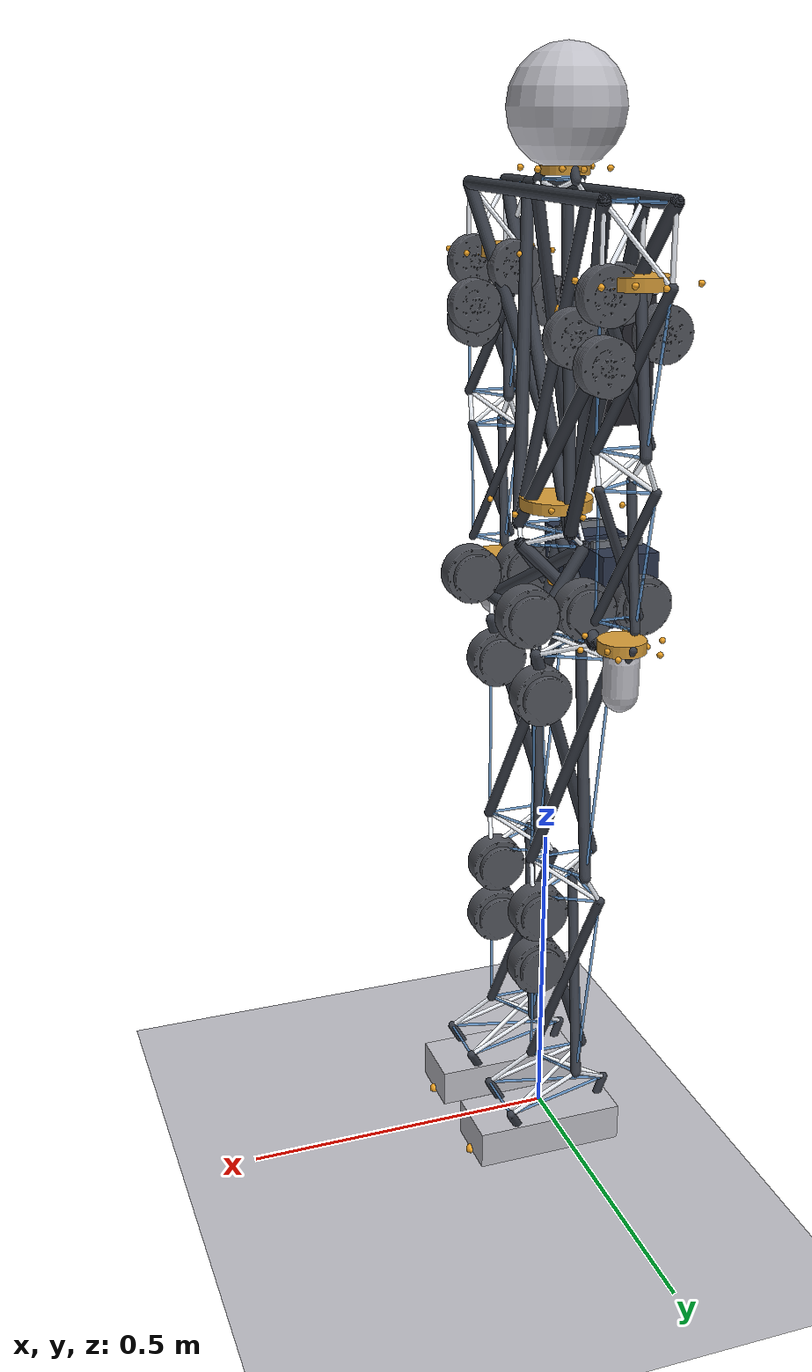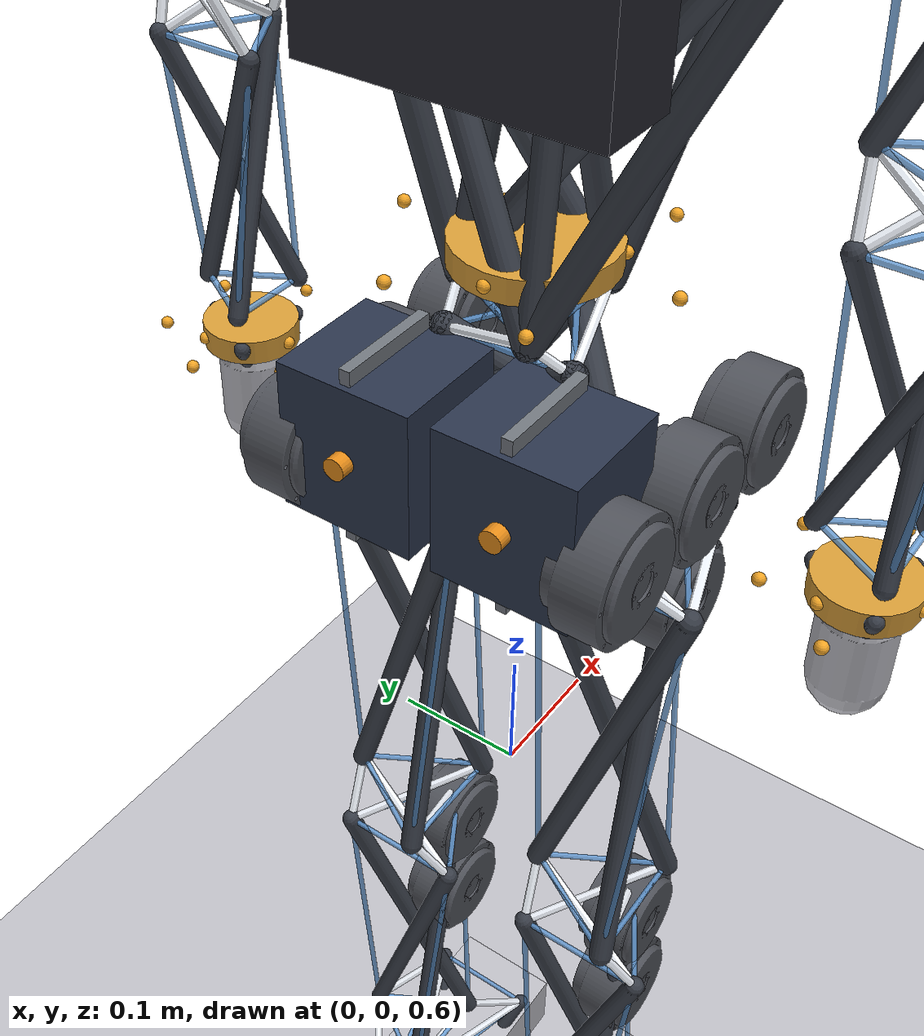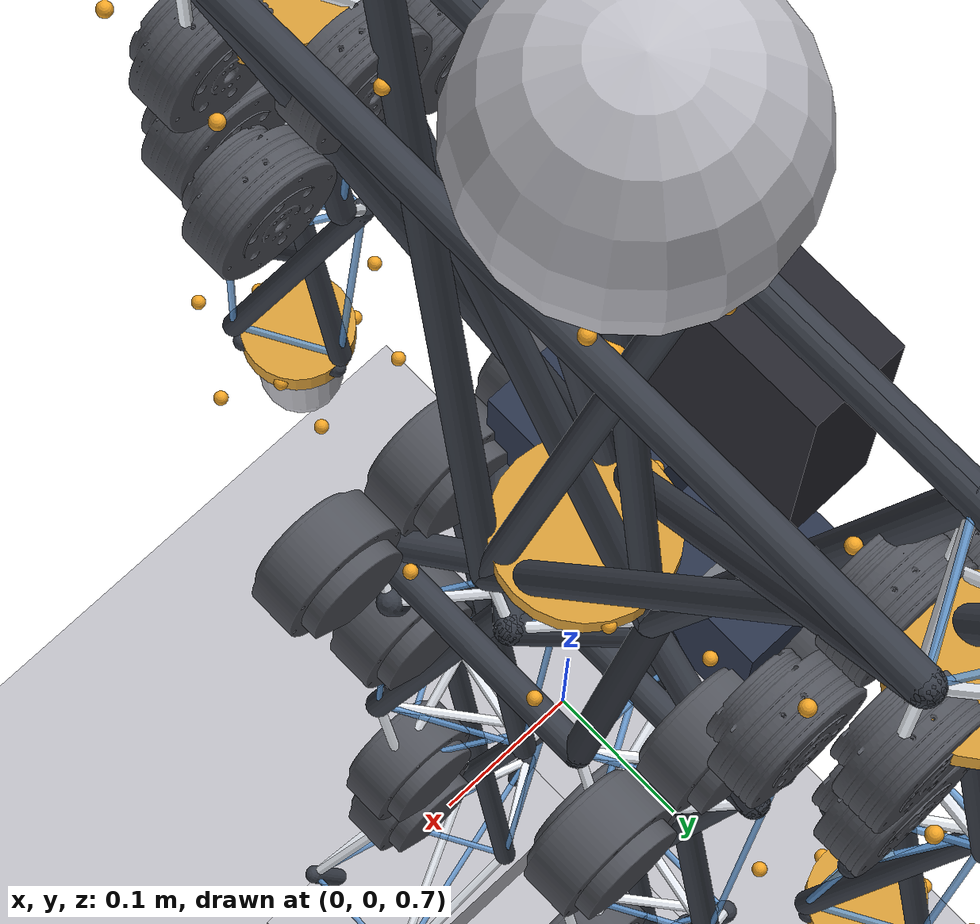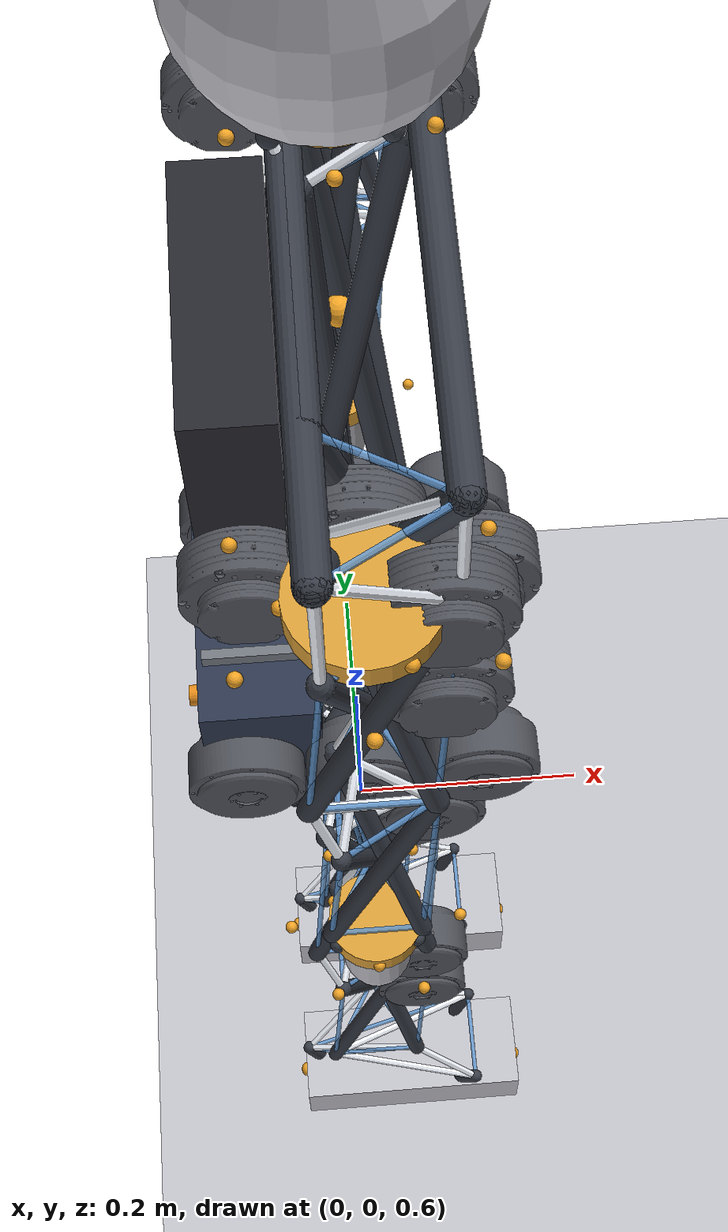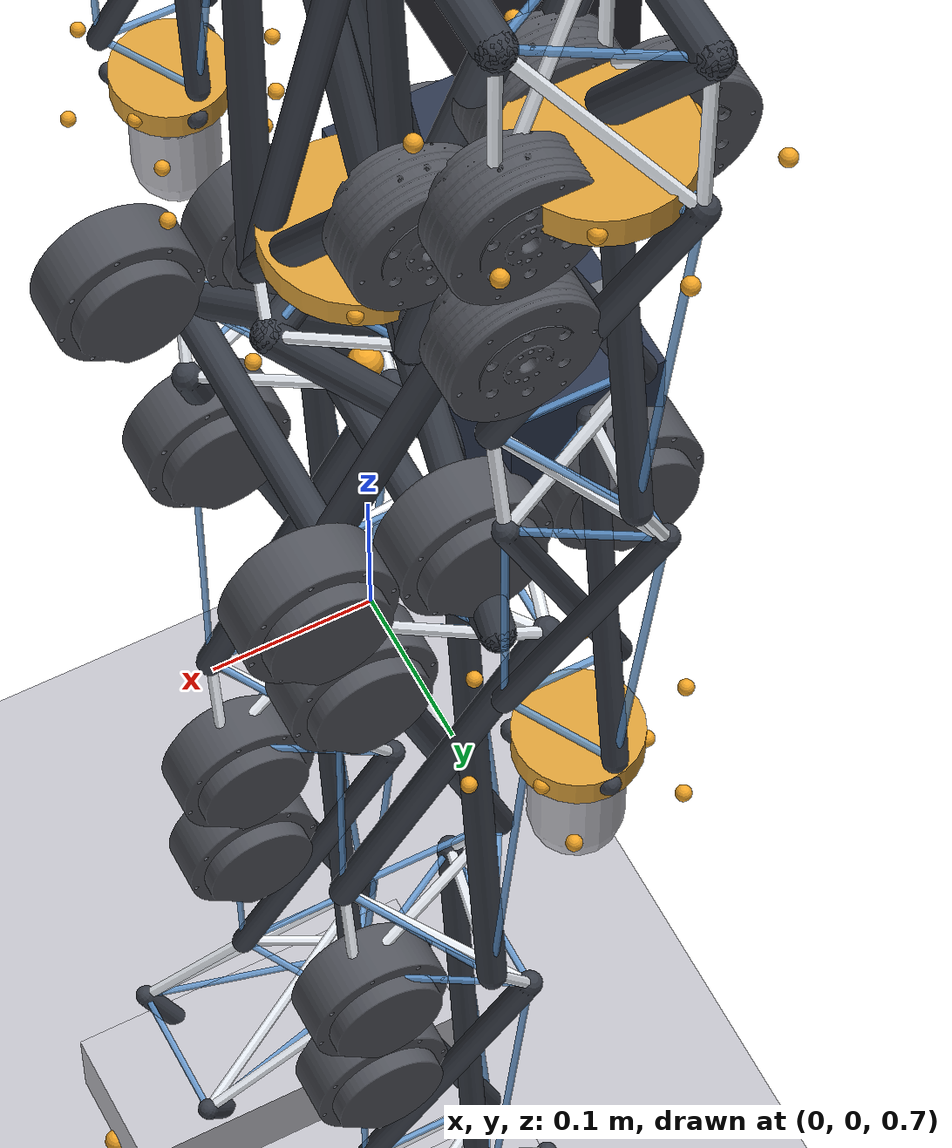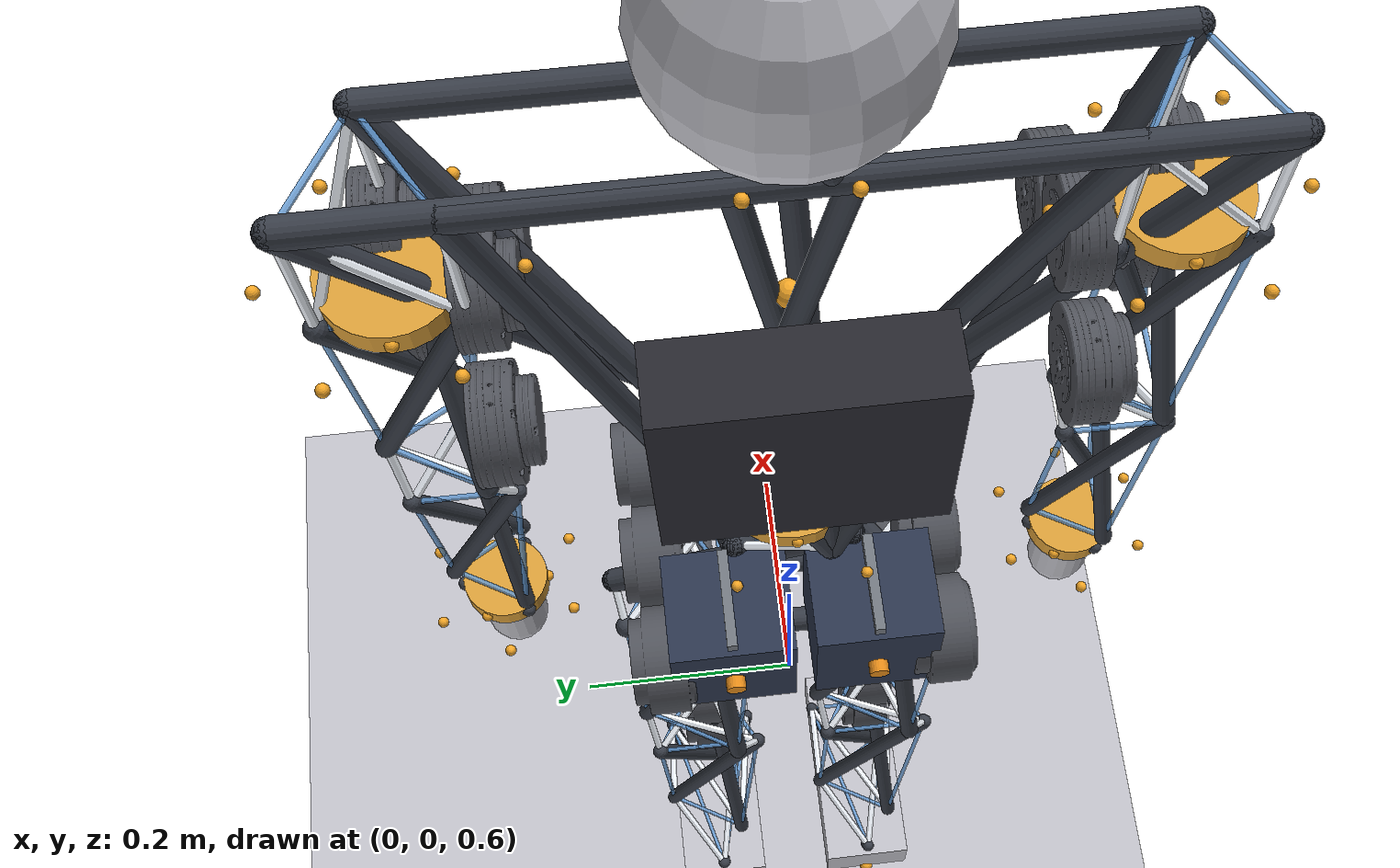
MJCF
<mujoco model="humanoid27_tensegrity">
  <compiler angle="radian" autolimits="true" meshdir="assets"/>
  <option timestep="0.004" integrator="implicitfast" solver="Newton" iterations="100"/>

  <default>
    <joint damping="2.0" armature="0.03" limited="true"/>
    <geom friction="1.0 0.005 0.0001" condim="3" contype="1" conaffinity="0"
          rgba="0.75 0.75 0.78 1"/>
    <site size="0.0045" rgba="0.95 0.65 0.15 0.95"/>
    <motor ctrllimited="true"/>
    <default class="strut">
      <geom type="capsule" rgba="0.22 0.24 0.28 1" contype="0" conaffinity="0"/>
    </default>
    <default class="wire">
      <tendon width="0.0035" rgba="0.95 0.97 1 1"/>
    </default>
    <default class="weave">
      <tendon width="0.0022" rgba="0.40 0.62 0.85 0.85"/>
    </default>
    <default class="drum">
      <geom rgba="0.85 0.62 0.22 1" contype="0" conaffinity="0" mass="0.02"/>
    </default>
    <default class="motormesh">
      <geom type="mesh" contype="0" conaffinity="0" rgba="0.32 0.33 0.36 1"/>
    </default>
  </default>

  <asset>
    <texture name="grid" type="2d" builtin="checker" rgb1="0.2 0.25 0.3" rgb2="0.3 0.35 0.4"
             width="512" height="512"/>
    <material name="grid" texture="grid" texrepeat="8 8" reflectance="0.1"/>
    <mesh name="ak70" file="ak70_10.stl"/>
    <mesh name="ak60" file="ak60_6.stl"/>
  </asset>

  <worldbody>
    <light pos="0 0 3" dir="0 0 -1" directional="true"/>
    <geom name="floor" type="plane" size="20 20 0.1" material="grid" contype="1" conaffinity="1"/>

    <body name="pelvis" pos="0 0 0.936">
      <freejoint name="root"/>
      <geom class="strut" size="0.01" fromto="3.796e-18 0.152 -0.055 -0.02767 -0.04754 0.06" mass="0.24444"/>
      <geom class="strut" size="0.01" fromto="3.796e-18 -0.028 -0.055 -0.02767 -0.04754 0.06" mass="0.24444"/>
      <geom class="strut" size="0.01" fromto="3.796e-18 0.152 -0.055 3.796e-18 -0.028 -0.055" mass="0.24444"/>
      <geom class="strut" size="0.01" fromto="-0.05369 0.059 -0.055 0.055 -0.000192 0.06" mass="0.24444"/>
      <geom class="strut" size="0.01" fromto="-0.05369 -0.121 -0.055 0.055 -0.000192 0.06" mass="0.24444"/>
      <geom class="strut" size="0.01" fromto="-0.05369 0.059 -0.055 -0.05369 -0.121 -0.055" mass="0.24444"/>
      <geom class="strut" size="0.01" fromto="0.05369 0.059 -0.055 -0.02733 0.04773 0.06" mass="0.24444"/>
      <geom class="strut" size="0.01" fromto="0.05369 -0.121 -0.055 -0.02733 0.04773 0.06" mass="0.24444"/>
      <geom class="strut" size="0.01" fromto="0.05369 0.059 -0.055 0.05369 -0.121 -0.055" mass="0.24444"/>
      <geom name="hip_motor_l_a" class="motormesh" mesh="ak70" pos="-0.09 0.115 -0.015" euler="1.5708 0 0" mass="0.56667"/>
      <geom name="hip_motor_l_b" class="motormesh" mesh="ak70" pos="0 0.115 -0.015" euler="1.5708 0 0" mass="0.56667"/>
      <geom name="hip_motor_l_c" class="motormesh" mesh="ak70" pos="0.09 0.115 -0.015" euler="1.5708 0 0" mass="0.56667"/>
      <geom name="hip_motor_r_a" class="motormesh" mesh="ak70" pos="-0.09 -0.115 -0.015" euler="1.5708 0 0" mass="0.56667"/>
      <geom name="hip_motor_r_b" class="motormesh" mesh="ak70" pos="0 -0.115 -0.015" euler="1.5708 0 0" mass="0.56667"/>
      <geom name="hip_motor_r_c" class="motormesh" mesh="ak70" pos="0.09 -0.115 -0.015" euler="1.5708 0 0" mass="0.56667"/>
      <site name="pelvis_site" pos="0 0 0" size="0.01"/>
      <site name="rt_pelvis_waist_0_a" pos="-0.02733 0.04773 0.06"/>
      <site name="rt_pelvis_waist_0_b" pos="-0.02767 -0.04754 0.06"/>
      <site name="rt_pelvis_waist_1_a" pos="-0.02767 -0.04754 0.06"/>
      <site name="rt_pelvis_waist_1_b" pos="0.055 -0.000192 0.06"/>
      <site name="rt_pelvis_waist_2_a" pos="0.055 -0.000192 0.06"/>
      <site name="rt_pelvis_waist_2_b" pos="-0.02733 0.04773 0.06"/>
      <site name="rt_pelvis_hip_l_0_a" pos="3.796e-18 0.152 -0.055"/>
      <site name="rt_pelvis_hip_l_0_b" pos="-0.05369 0.059 -0.055"/>
      <site name="rt_pelvis_hip_l_1_a" pos="-0.05369 0.059 -0.055"/>
      <site name="rt_pelvis_hip_l_1_b" pos="0.05369 0.059 -0.055"/>
      <site name="rt_pelvis_hip_l_2_a" pos="0.05369 0.059 -0.055"/>
      <site name="rt_pelvis_hip_l_2_b" pos="3.796e-18 0.152 -0.055"/>
      <site name="rt_pelvis_hip_r_0_a" pos="3.796e-18 -0.028 -0.055"/>
      <site name="rt_pelvis_hip_r_0_b" pos="-0.05369 -0.121 -0.055"/>
      <site name="rt_pelvis_hip_r_1_a" pos="-0.05369 -0.121 -0.055"/>
      <site name="rt_pelvis_hip_r_1_b" pos="0.05369 -0.121 -0.055"/>
      <site name="rt_pelvis_hip_r_2_a" pos="0.05369 -0.121 -0.055"/>
      <site name="rt_pelvis_hip_r_2_b" pos="3.796e-18 -0.028 -0.055"/>
      <site name="hip_l0_a" pos="3.796e-18 0.152 -0.055"/>
      <site name="hip_l1_a" pos="-0.05369 0.059 -0.055"/>
      <site name="hip_l2_a" pos="0.05369 0.059 -0.055"/>
      <site name="hip_l3_a" pos="3.796e-18 0.152 -0.055"/>
      <site name="hip_l4_a" pos="-0.05369 0.059 -0.055"/>
      <site name="hip_l5_a" pos="0.05369 0.059 -0.055"/>
      <site name="hip_l6_a" pos="3.796e-18 0.152 -0.055"/>
      <site name="hip_l7_a" pos="-0.05369 0.059 -0.055"/>
      <site name="hip_l8_a" pos="0.05369 0.059 -0.055"/>
      <site name="hip_r0_a" pos="3.796e-18 -0.028 -0.055"/>
      <site name="hip_r1_a" pos="-0.05369 -0.121 -0.055"/>
      <site name="hip_r2_a" pos="0.05369 -0.121 -0.055"/>
      <site name="hip_r3_a" pos="3.796e-18 -0.028 -0.055"/>
      <site name="hip_r4_a" pos="-0.05369 -0.121 -0.055"/>
      <site name="hip_r5_a" pos="0.05369 -0.121 -0.055"/>
      <site name="hip_r6_a" pos="3.796e-18 -0.028 -0.055"/>
      <site name="hip_r7_a" pos="-0.05369 -0.121 -0.055"/>
      <site name="hip_r8_a" pos="0.05369 -0.121 -0.055"/>
      <site name="waist0_a" pos="-0.02733 0.04773 0.06"/>
      <site name="waist1_a" pos="-0.02767 -0.04754 0.06"/>
      <site name="waist2_a" pos="0.055 -0.000192 0.06"/>
      <site name="waist3_a" pos="-0.02733 0.04773 0.06"/>
      <site name="waist4_a" pos="-0.02767 -0.04754 0.06"/>
      <site name="waist5_a" pos="0.055 -0.000192 0.06"/>
      <site name="waist_yawdrum0_a" pos="-0.02733 0.04773 0.06"/>
      <site name="waist_yawdrum1_a" pos="-0.02767 -0.04754 0.06"/>
      <site name="waist_yawdrum2_a" pos="0.055 -0.000192 0.06"/>
      <site name="waist_yawdrum3_a" pos="-0.02733 0.04773 0.06"/>
      <site name="waist_yawdrum4_a" pos="-0.02767 -0.04754 0.06"/>
      <site name="waist_yawdrum5_a" pos="0.055 -0.000192 0.06"/>
      <body name="battery_l" pos="-0.075 0.058 0.005">
        <geom name="battery_l_cells" type="box" size="0.045 0.05 0.055" mass="2.5" rgba="0.17 0.21 0.30 1"/>
        <geom name="battery_l_rail_t" type="box" size="0.0405 0.004 0.006" pos="0 0 0.06" mass="0" rgba="0.45 0.47 0.5 1"/>
        <geom name="battery_l_rail_b" type="box" size="0.0405 0.004 0.006" pos="0 0 -0.06" mass="0" rgba="0.45 0.47 0.5 1"/>
        <geom name="battery_l_latch" type="cylinder" size="0.008 0.006" pos="-0.049 0 0" euler="0 1.5708 0" mass="0" rgba="0.9 0.55 0.1 1"/>
      </body>
      <body name="battery_r" pos="-0.075 -0.058 0.005">
        <geom name="battery_r_cells" type="box" size="0.045 0.05 0.055" mass="2.5" rgba="0.17 0.21 0.30 1"/>
        <geom name="battery_r_rail_t" type="box" size="0.0405 0.004 0.006" pos="0 0 0.06" mass="0" rgba="0.45 0.47 0.5 1"/>
        <geom name="battery_r_rail_b" type="box" size="0.0405 0.004 0.006" pos="0 0 -0.06" mass="0" rgba="0.45 0.47 0.5 1"/>
        <geom name="battery_r_latch" type="cylinder" size="0.008 0.006" pos="-0.049 0 0" euler="0 1.5708 0" mass="0" rgba="0.9 0.55 0.1 1"/>
      </body>

      <body name="thigh_l" pos="0 0.09 -0.06">
        <joint name="hip_yaw_l"   axis="0 0 1" range="-0.8 0.8"/>
        <joint name="hip_roll_l"  axis="1 0 0" range="-0.4 0.8"/>
        <joint name="hip_pitch_l" axis="0 1 0" range="-2.0 0.7"/>
        <geom class="strut" size="0.009" fromto="3.674e-18 0.06 -0.375 -0.0327 -0.05618 -0.025" mass="0.11667"/>
        <geom class="strut" size="0.009" fromto="-0.05196 -0.03 -0.375 0.065 -0.0002269 -0.025" mass="0.11667"/>
        <geom class="strut" size="0.009" fromto="0.05196 -0.03 -0.375 -0.0323 0.0564 -0.025" mass="0.11667"/>
        <geom name="knee_motor_l" class="motormesh" mesh="ak70" pos="0.055 0 -0.09" euler="1.5708 0 0" mass="0.7"/>
        <site name="pw_thigh_l_bottop_b0_a" pos="3.674e-18 0.06 -0.375"/>
        <site name="pw_thigh_l_bottop_b0_b" pos="-0.05196 -0.03 -0.375"/>
        <site name="pw_thigh_l_bottop_t0_a" pos="-0.0323 0.0564 -0.025"/>
        <site name="pw_thigh_l_bottop_t0_b" pos="-0.0327 -0.05618 -0.025"/>
        <site name="pw_thigh_l_bottop_v0_a" pos="3.674e-18 0.06 -0.375"/>
        <site name="pw_thigh_l_bottop_v0_b" pos="-0.0323 0.0564 -0.025"/>
        <site name="pw_thigh_l_bottop_b1_a" pos="-0.05196 -0.03 -0.375"/>
        <site name="pw_thigh_l_bottop_b1_b" pos="0.05196 -0.03 -0.375"/>
        <site name="pw_thigh_l_bottop_t1_a" pos="-0.0327 -0.05618 -0.025"/>
        <site name="pw_thigh_l_bottop_t1_b" pos="0.065 -0.0002269 -0.025"/>
        <site name="pw_thigh_l_bottop_v1_a" pos="-0.05196 -0.03 -0.375"/>
        <site name="pw_thigh_l_bottop_v1_b" pos="-0.0327 -0.05618 -0.025"/>
        <site name="pw_thigh_l_bottop_b2_a" pos="0.05196 -0.03 -0.375"/>
        <site name="pw_thigh_l_bottop_b2_b" pos="3.674e-18 0.06 -0.375"/>
        <site name="pw_thigh_l_bottop_t2_a" pos="0.065 -0.0002269 -0.025"/>
        <site name="pw_thigh_l_bottop_t2_b" pos="-0.0323 0.0564 -0.025"/>
        <site name="pw_thigh_l_bottop_v2_a" pos="0.05196 -0.03 -0.375"/>
        <site name="pw_thigh_l_bottop_v2_b" pos="0.065 -0.0002269 -0.025"/>
        <site name="hip_l0_b" pos="-0.0323 0.0564 -0.025"/>
        <site name="hip_l1_b" pos="-0.0327 -0.05618 -0.025"/>
        <site name="hip_l2_b" pos="0.065 -0.0002269 -0.025"/>
        <site name="hip_l3_b" pos="-0.0327 -0.05618 -0.025"/>
        <site name="hip_l4_b" pos="0.065 -0.0002269 -0.025"/>
        <site name="hip_l5_b" pos="-0.0323 0.0564 -0.025"/>
        <site name="hip_l6_b" pos="0.065 -0.0002269 -0.025"/>
        <site name="hip_l7_b" pos="-0.0323 0.0564 -0.025"/>
        <site name="hip_l8_b" pos="-0.0327 -0.05618 -0.025"/>
        <site name="knee_l0_a" pos="3.674e-18 0.06 -0.375"/>
        <site name="knee_l1_a" pos="-0.05196 -0.03 -0.375"/>
        <site name="knee_l2_a" pos="0.05196 -0.03 -0.375"/>
        <site name="knee_l3_a" pos="3.674e-18 0.06 -0.375"/>
        <site name="knee_l4_a" pos="-0.05196 -0.03 -0.375"/>
        <site name="knee_l5_a" pos="0.05196 -0.03 -0.375"/>
        <body name="shank_l" pos="0 0 -0.40">
          <joint name="knee_l" axis="0 1 0" range="-0.05 2.4"/>
          <geom class="strut" size="0.008" fromto="3.184e-18 0.052 -0.33 -0.03018 -0.05186 -0.025" mass="0.1"/>
          <geom class="strut" size="0.008" fromto="-0.04503 -0.026 -0.33 0.06 -0.0002094 -0.025" mass="0.1"/>
          <geom class="strut" size="0.008" fromto="0.04503 -0.026 -0.33 -0.02982 0.05207 -0.025" mass="0.1"/>
          <geom name="ankle_motor_l_a" class="motormesh" mesh="ak70" pos="0.05 0 -0.055" euler="1.5708 0 0" mass="0.7"/>
          <geom name="ankle_motor_l_b" class="motormesh" mesh="ak70" pos="0.05 0 -0.15" euler="1.5708 0 0" mass="0.7"/>
          <site name="pw_shank_l_bottop_b0_a" pos="3.184e-18 0.052 -0.33"/>
          <site name="pw_shank_l_bottop_b0_b" pos="-0.04503 -0.026 -0.33"/>
          <site name="pw_shank_l_bottop_t0_a" pos="-0.02982 0.05207 -0.025"/>
          <site name="pw_shank_l_bottop_t0_b" pos="-0.03018 -0.05186 -0.025"/>
          <site name="pw_shank_l_bottop_v0_a" pos="3.184e-18 0.052 -0.33"/>
          <site name="pw_shank_l_bottop_v0_b" pos="-0.02982 0.05207 -0.025"/>
          <site name="pw_shank_l_bottop_b1_a" pos="-0.04503 -0.026 -0.33"/>
          <site name="pw_shank_l_bottop_b1_b" pos="0.04503 -0.026 -0.33"/>
          <site name="pw_shank_l_bottop_t1_a" pos="-0.03018 -0.05186 -0.025"/>
          <site name="pw_shank_l_bottop_t1_b" pos="0.06 -0.0002094 -0.025"/>
          <site name="pw_shank_l_bottop_v1_a" pos="-0.04503 -0.026 -0.33"/>
          <site name="pw_shank_l_bottop_v1_b" pos="-0.03018 -0.05186 -0.025"/>
          <site name="pw_shank_l_bottop_b2_a" pos="0.04503 -0.026 -0.33"/>
          <site name="pw_shank_l_bottop_b2_b" pos="3.184e-18 0.052 -0.33"/>
          <site name="pw_shank_l_bottop_t2_a" pos="0.06 -0.0002094 -0.025"/>
          <site name="pw_shank_l_bottop_t2_b" pos="-0.02982 0.05207 -0.025"/>
          <site name="pw_shank_l_bottop_v2_a" pos="0.04503 -0.026 -0.33"/>
          <site name="pw_shank_l_bottop_v2_b" pos="0.06 -0.0002094 -0.025"/>
          <site name="knee_l0_b" pos="-0.02982 0.05207 -0.025"/>
          <site name="knee_l1_b" pos="-0.03018 -0.05186 -0.025"/>
          <site name="knee_l2_b" pos="0.06 -0.0002094 -0.025"/>
          <site name="knee_l3_b" pos="-0.03018 -0.05186 -0.025"/>
          <site name="knee_l4_b" pos="0.06 -0.0002094 -0.025"/>
          <site name="knee_l5_b" pos="-0.02982 0.05207 -0.025"/>
          <site name="ankle_l0_a" pos="3.184e-18 0.052 -0.33"/>
          <site name="ankle_l1_a" pos="-0.04503 -0.026 -0.33"/>
          <site name="ankle_l2_a" pos="0.04503 -0.026 -0.33"/>
          <site name="ankle_l3_a" pos="3.184e-18 0.052 -0.33"/>
          <site name="ankle_l4_a" pos="-0.04503 -0.026 -0.33"/>
          <site name="ankle_l5_a" pos="0.04503 -0.026 -0.33"/>
          <body name="foot_l" pos="0 0 -0.40">
            <joint name="ankle_pitch_l" axis="0 1 0" range="-0.9 0.9"/>
            <joint name="ankle_roll_l"  axis="1 0 0" range="-0.4 0.4"/>
            <geom name="foot_l_geom" type="box" pos="0.04 0 -0.045" size="0.12 0.05 0.03" mass="0.40"/>
            <geom class="strut" size="0.007" fromto="-0.075 0 0.012 -0.06375 0 -0.018" mass="0"/>
            <geom class="strut" size="0.007" fromto="0.11 0.048 0.012 0.0935 0.0384 -0.018" mass="0"/>
            <geom class="strut" size="0.007" fromto="0.11 -0.048 0.012 0.0935 -0.0384 -0.018" mass="0"/>
            <site name="foot_l_site" pos="0.04 0 -0.075" size="0.01"/>
            <site name="sp2" pos="0.16 0 -0.075" size="0.008"/>
            <site name="sp3" pos="-0.08 0 -0.075" size="0.008"/>
            <site name="rt_foot_l_top_0_a" pos="-0.075 0 0.012"/>
            <site name="rt_foot_l_top_0_b" pos="0.11 0.048 0.012"/>
            <site name="rt_foot_l_top_1_a" pos="0.11 0.048 0.012"/>
            <site name="rt_foot_l_top_1_b" pos="0.11 -0.048 0.012"/>
            <site name="rt_foot_l_top_2_a" pos="0.11 -0.048 0.012"/>
            <site name="rt_foot_l_top_2_b" pos="-0.075 0 0.012"/>
            <site name="ankle_l0_b" pos="-0.075 0 0.012"/>
            <site name="ankle_l1_b" pos="0.11 0.048 0.012"/>
            <site name="ankle_l2_b" pos="0.11 -0.048 0.012"/>
            <site name="ankle_l3_b" pos="0.11 0.048 0.012"/>
            <site name="ankle_l4_b" pos="0.11 -0.048 0.012"/>
            <site name="ankle_l5_b" pos="-0.075 0 0.012"/>
          </body>
        </body>
      </body>
      <body name="thigh_r" pos="0 -0.09 -0.06">
        <joint name="hip_yaw_r"   axis="0 0 1" range="-0.8 0.8"/>
        <joint name="hip_roll_r"  axis="1 0 0" range="-0.8 0.4"/>
        <joint name="hip_pitch_r" axis="0 1 0" range="-2.0 0.7"/>
        <geom class="strut" size="0.009" fromto="3.674e-18 0.06 -0.375 -0.0327 -0.05618 -0.025" mass="0.11667"/>
        <geom class="strut" size="0.009" fromto="-0.05196 -0.03 -0.375 0.065 -0.0002269 -0.025" mass="0.11667"/>
        <geom class="strut" size="0.009" fromto="0.05196 -0.03 -0.375 -0.0323 0.0564 -0.025" mass="0.11667"/>
        <geom name="knee_motor_r" class="motormesh" mesh="ak70" pos="0.055 0 -0.09" euler="1.5708 0 0" mass="0.7"/>
        <site name="pw_thigh_r_bottop_b0_a" pos="3.674e-18 0.06 -0.375"/>
        <site name="pw_thigh_r_bottop_b0_b" pos="-0.05196 -0.03 -0.375"/>
        <site name="pw_thigh_r_bottop_t0_a" pos="-0.0323 0.0564 -0.025"/>
        <site name="pw_thigh_r_bottop_t0_b" pos="-0.0327 -0.05618 -0.025"/>
        <site name="pw_thigh_r_bottop_v0_a" pos="3.674e-18 0.06 -0.375"/>
        <site name="pw_thigh_r_bottop_v0_b" pos="-0.0323 0.0564 -0.025"/>
        <site name="pw_thigh_r_bottop_b1_a" pos="-0.05196 -0.03 -0.375"/>
        <site name="pw_thigh_r_bottop_b1_b" pos="0.05196 -0.03 -0.375"/>
        <site name="pw_thigh_r_bottop_t1_a" pos="-0.0327 -0.05618 -0.025"/>
        <site name="pw_thigh_r_bottop_t1_b" pos="0.065 -0.0002269 -0.025"/>
        <site name="pw_thigh_r_bottop_v1_a" pos="-0.05196 -0.03 -0.375"/>
        <site name="pw_thigh_r_bottop_v1_b" pos="-0.0327 -0.05618 -0.025"/>
        <site name="pw_thigh_r_bottop_b2_a" pos="0.05196 -0.03 -0.375"/>
        <site name="pw_thigh_r_bottop_b2_b" pos="3.674e-18 0.06 -0.375"/>
        <site name="pw_thigh_r_bottop_t2_a" pos="0.065 -0.0002269 -0.025"/>
        <site name="pw_thigh_r_bottop_t2_b" pos="-0.0323 0.0564 -0.025"/>
        <site name="pw_thigh_r_bottop_v2_a" pos="0.05196 -0.03 -0.375"/>
        <site name="pw_thigh_r_bottop_v2_b" pos="0.065 -0.0002269 -0.025"/>
        <site name="hip_r0_b" pos="-0.0323 0.0564 -0.025"/>
        <site name="hip_r1_b" pos="-0.0327 -0.05618 -0.025"/>
        <site name="hip_r2_b" pos="0.065 -0.0002269 -0.025"/>
        <site name="hip_r3_b" pos="-0.0327 -0.05618 -0.025"/>
        <site name="hip_r4_b" pos="0.065 -0.0002269 -0.025"/>
        <site name="hip_r5_b" pos="-0.0323 0.0564 -0.025"/>
        <site name="hip_r6_b" pos="0.065 -0.0002269 -0.025"/>
        <site name="hip_r7_b" pos="-0.0323 0.0564 -0.025"/>
        <site name="hip_r8_b" pos="-0.0327 -0.05618 -0.025"/>
        <site name="knee_r0_a" pos="3.674e-18 0.06 -0.375"/>
        <site name="knee_r1_a" pos="-0.05196 -0.03 -0.375"/>
        <site name="knee_r2_a" pos="0.05196 -0.03 -0.375"/>
        <site name="knee_r3_a" pos="3.674e-18 0.06 -0.375"/>
        <site name="knee_r4_a" pos="-0.05196 -0.03 -0.375"/>
        <site name="knee_r5_a" pos="0.05196 -0.03 -0.375"/>
        <body name="shank_r" pos="0 0 -0.40">
          <joint name="knee_r" axis="0 1 0" range="-0.05 2.4"/>
          <geom class="strut" size="0.008" fromto="3.184e-18 0.052 -0.33 -0.03018 -0.05186 -0.025" mass="0.1"/>
          <geom class="strut" size="0.008" fromto="-0.04503 -0.026 -0.33 0.06 -0.0002094 -0.025" mass="0.1"/>
          <geom class="strut" size="0.008" fromto="0.04503 -0.026 -0.33 -0.02982 0.05207 -0.025" mass="0.1"/>
          <geom name="ankle_motor_r_a" class="motormesh" mesh="ak70" pos="0.05 0 -0.055" euler="1.5708 0 0" mass="0.7"/>
          <geom name="ankle_motor_r_b" class="motormesh" mesh="ak70" pos="0.05 0 -0.15" euler="1.5708 0 0" mass="0.7"/>
          <site name="pw_shank_r_bottop_b0_a" pos="3.184e-18 0.052 -0.33"/>
          <site name="pw_shank_r_bottop_b0_b" pos="-0.04503 -0.026 -0.33"/>
          <site name="pw_shank_r_bottop_t0_a" pos="-0.02982 0.05207 -0.025"/>
          <site name="pw_shank_r_bottop_t0_b" pos="-0.03018 -0.05186 -0.025"/>
          <site name="pw_shank_r_bottop_v0_a" pos="3.184e-18 0.052 -0.33"/>
          <site name="pw_shank_r_bottop_v0_b" pos="-0.02982 0.05207 -0.025"/>
          <site name="pw_shank_r_bottop_b1_a" pos="-0.04503 -0.026 -0.33"/>
          <site name="pw_shank_r_bottop_b1_b" pos="0.04503 -0.026 -0.33"/>
          <site name="pw_shank_r_bottop_t1_a" pos="-0.03018 -0.05186 -0.025"/>
          <site name="pw_shank_r_bottop_t1_b" pos="0.06 -0.0002094 -0.025"/>
          <site name="pw_shank_r_bottop_v1_a" pos="-0.04503 -0.026 -0.33"/>
          <site name="pw_shank_r_bottop_v1_b" pos="-0.03018 -0.05186 -0.025"/>
          <site name="pw_shank_r_bottop_b2_a" pos="0.04503 -0.026 -0.33"/>
          <site name="pw_shank_r_bottop_b2_b" pos="3.184e-18 0.052 -0.33"/>
          <site name="pw_shank_r_bottop_t2_a" pos="0.06 -0.0002094 -0.025"/>
          <site name="pw_shank_r_bottop_t2_b" pos="-0.02982 0.05207 -0.025"/>
          <site name="pw_shank_r_bottop_v2_a" pos="0.04503 -0.026 -0.33"/>
          <site name="pw_shank_r_bottop_v2_b" pos="0.06 -0.0002094 -0.025"/>
          <site name="knee_r0_b" pos="-0.02982 0.05207 -0.025"/>
          <site name="knee_r1_b" pos="-0.03018 -0.05186 -0.025"/>
          <site name="knee_r2_b" pos="0.06 -0.0002094 -0.025"/>
          <site name="knee_r3_b" pos="-0.03018 -0.05186 -0.025"/>
          <site name="knee_r4_b" pos="0.06 -0.0002094 -0.025"/>
          <site name="knee_r5_b" pos="-0.02982 0.05207 -0.025"/>
          <site name="ankle_r0_a" pos="3.184e-18 0.052 -0.33"/>
          <site name="ankle_r1_a" pos="-0.04503 -0.026 -0.33"/>
          <site name="ankle_r2_a" pos="0.04503 -0.026 -0.33"/>
          <site name="ankle_r3_a" pos="3.184e-18 0.052 -0.33"/>
          <site name="ankle_r4_a" pos="-0.04503 -0.026 -0.33"/>
          <site name="ankle_r5_a" pos="0.04503 -0.026 -0.33"/>
          <body name="foot_r" pos="0 0 -0.40">
            <joint name="ankle_pitch_r" axis="0 1 0" range="-0.9 0.9"/>
            <joint name="ankle_roll_r"  axis="1 0 0" range="-0.4 0.4"/>
            <geom name="foot_r_geom" type="box" pos="0.04 0 -0.045" size="0.12 0.05 0.03" mass="0.40"/>
            <geom class="strut" size="0.007" fromto="-0.075 0 0.012 -0.06375 0 -0.018" mass="0"/>
            <geom class="strut" size="0.007" fromto="0.11 0.048 0.012 0.0935 0.0384 -0.018" mass="0"/>
            <geom class="strut" size="0.007" fromto="0.11 -0.048 0.012 0.0935 -0.0384 -0.018" mass="0"/>
            <site name="foot_r_site" pos="0.04 0 -0.075" size="0.01"/>
            <site name="sp0" pos="0.16 0 -0.075" size="0.008"/>
            <site name="sp1" pos="-0.08 0 -0.075" size="0.008"/>
            <site name="rt_foot_r_top_0_a" pos="-0.075 0 0.012"/>
            <site name="rt_foot_r_top_0_b" pos="0.11 0.048 0.012"/>
            <site name="rt_foot_r_top_1_a" pos="0.11 0.048 0.012"/>
            <site name="rt_foot_r_top_1_b" pos="0.11 -0.048 0.012"/>
            <site name="rt_foot_r_top_2_a" pos="0.11 -0.048 0.012"/>
            <site name="rt_foot_r_top_2_b" pos="-0.075 0 0.012"/>
            <site name="ankle_r0_b" pos="-0.075 0 0.012"/>
            <site name="ankle_r1_b" pos="0.11 0.048 0.012"/>
            <site name="ankle_r2_b" pos="0.11 -0.048 0.012"/>
            <site name="ankle_r3_b" pos="0.11 0.048 0.012"/>
            <site name="ankle_r4_b" pos="0.11 -0.048 0.012"/>
            <site name="ankle_r5_b" pos="-0.075 0 0.012"/>
          </body>
        </body>
      </body>
      <body name="torso" pos="0 0 0.10">
        <joint name="waist_yaw"   axis="0 0 1" range="-0.7 0.7"/>
        <joint name="waist_pitch" axis="0 1 0" range="-0.5 0.6"/>
        <joint name="waist_roll"  axis="1 0 0" range="-0.4 0.4"/>
        <geom class="strut" size="0.01" fromto="3.368e-18 0.055 -0.015 -0.02616 0.1951 0.465" mass="0.375"/>
        <geom class="strut" size="0.01" fromto="3.368e-18 0.055 -0.015 -0.02616 -0.2849 0.465" mass="0.375"/>
        <geom class="strut" size="0.01" fromto="-0.02584 0.2851 0.465 -0.02584 -0.1949 0.465" mass="0.375"/>
        <geom class="strut" size="0.009" fromto="3.368e-18 0.055 -0.015 -0.02012 -0.03457 0.455" mass="0.375"/>
        <geom class="strut" size="0.01" fromto="-0.04763 -0.0275 -0.015 0.052 0.2398 0.465" mass="0.375"/>
        <geom class="strut" size="0.01" fromto="-0.04763 -0.0275 -0.015 0.052 -0.2402 0.465" mass="0.375"/>
        <geom class="strut" size="0.01" fromto="-0.02616 0.1951 0.465 -0.02616 -0.2849 0.465" mass="0.375"/>
        <geom class="strut" size="0.009" fromto="-0.04763 -0.0275 -0.015 0.04 -0.0001396 0.455" mass="0.375"/>
        <geom class="strut" size="0.01" fromto="0.04763 -0.0275 -0.015 -0.02584 0.2851 0.465" mass="0.375"/>
        <geom class="strut" size="0.01" fromto="0.04763 -0.0275 -0.015 -0.02584 -0.1949 0.465" mass="0.375"/>
        <geom class="strut" size="0.01" fromto="0.052 0.2398 0.465 0.052 -0.2402 0.465" mass="0.375"/>
        <geom class="strut" size="0.009" fromto="0.04763 -0.0275 -0.015 -0.01988 0.03471 0.455" mass="0.375"/>
        <geom name="waist_yawdrum_drum" class="drum" type="cylinder" size="0.055 0.009" pos="0 0 0.02"/>
        <geom name="vest" type="box" pos="-0.07 0 0.24" size="0.03 0.10 0.09" rgba="0.15 0.15 0.18 1" mass="1.44"/>
        <geom name="sh_motor_l_a" class="motormesh" mesh="ak60" pos="0 0.185 0.345" euler="1.5708 0 0" mass="0.31"/>
        <geom name="sh_motor_l_b" class="motormesh" mesh="ak60" pos="0.065 0.185 0.29" euler="1.5708 0 0" mass="0.31"/>
        <geom name="sh_motor_l_c" class="motormesh" mesh="ak60" pos="-0.065 0.185 0.29" euler="1.5708 0 0" mass="0.31"/>
        <geom name="sh_motor_r_a" class="motormesh" mesh="ak60" pos="0 -0.185 0.345" euler="1.5708 0 0" mass="0.31"/>
        <geom name="sh_motor_r_b" class="motormesh" mesh="ak60" pos="0.065 -0.185 0.29" euler="1.5708 0 0" mass="0.31"/>
        <geom name="sh_motor_r_c" class="motormesh" mesh="ak60" pos="-0.065 -0.185 0.29" euler="1.5708 0 0" mass="0.31"/>
        <site name="imu" pos="0 0 0.30" size="0.01"/>
        <site name="rt_torso_waist_0_a" pos="3.368e-18 0.055 -0.015"/>
        <site name="rt_torso_waist_0_b" pos="-0.04763 -0.0275 -0.015"/>
        <site name="rt_torso_waist_1_a" pos="-0.04763 -0.0275 -0.015"/>
        <site name="rt_torso_waist_1_b" pos="0.04763 -0.0275 -0.015"/>
        <site name="rt_torso_waist_2_a" pos="0.04763 -0.0275 -0.015"/>
        <site name="rt_torso_waist_2_b" pos="3.368e-18 0.055 -0.015"/>
        <site name="rt_torso_sh_l_0_a" pos="-0.02584 0.2851 0.465"/>
        <site name="rt_torso_sh_l_0_b" pos="-0.02616 0.1951 0.465"/>
        <site name="rt_torso_sh_l_1_a" pos="-0.02616 0.1951 0.465"/>
        <site name="rt_torso_sh_l_1_b" pos="0.052 0.2398 0.465"/>
        <site name="rt_torso_sh_l_2_a" pos="0.052 0.2398 0.465"/>
        <site name="rt_torso_sh_l_2_b" pos="-0.02584 0.2851 0.465"/>
        <site name="rt_torso_sh_r_0_a" pos="-0.02584 -0.1949 0.465"/>
        <site name="rt_torso_sh_r_0_b" pos="-0.02616 -0.2849 0.465"/>
        <site name="rt_torso_sh_r_1_a" pos="-0.02616 -0.2849 0.465"/>
        <site name="rt_torso_sh_r_1_b" pos="0.052 -0.2402 0.465"/>
        <site name="rt_torso_sh_r_2_a" pos="0.052 -0.2402 0.465"/>
        <site name="rt_torso_sh_r_2_b" pos="-0.02584 -0.1949 0.465"/>
        <site name="rt_torso_neck_0_a" pos="-0.01988 0.03471 0.455"/>
        <site name="rt_torso_neck_0_b" pos="-0.02012 -0.03457 0.455"/>
        <site name="rt_torso_neck_1_a" pos="-0.02012 -0.03457 0.455"/>
        <site name="rt_torso_neck_1_b" pos="0.04 -0.0001396 0.455"/>
        <site name="rt_torso_neck_2_a" pos="0.04 -0.0001396 0.455"/>
        <site name="rt_torso_neck_2_b" pos="-0.01988 0.03471 0.455"/>
        <site name="shoulder_l0_a" pos="-0.02584 0.2851 0.465"/>
        <site name="shoulder_l1_a" pos="-0.02616 0.1951 0.465"/>
        <site name="shoulder_l2_a" pos="0.052 0.2398 0.465"/>
        <site name="shoulder_l3_a" pos="-0.02584 0.2851 0.465"/>
        <site name="shoulder_l4_a" pos="-0.02616 0.1951 0.465"/>
        <site name="shoulder_l5_a" pos="0.052 0.2398 0.465"/>
        <site name="shoulder_yawdrum_l0_a" pos="-0.02584 0.2851 0.465"/>
        <site name="shoulder_yawdrum_l1_a" pos="-0.02616 0.1951 0.465"/>
        <site name="shoulder_yawdrum_l2_a" pos="0.052 0.2398 0.465"/>
        <site name="shoulder_yawdrum_l3_a" pos="-0.02584 0.2851 0.465"/>
        <site name="shoulder_yawdrum_l4_a" pos="-0.02616 0.1951 0.465"/>
        <site name="shoulder_yawdrum_l5_a" pos="0.052 0.2398 0.465"/>
        <site name="shoulder_r0_a" pos="-0.02584 -0.1949 0.465"/>
        <site name="shoulder_r1_a" pos="-0.02616 -0.2849 0.465"/>
        <site name="shoulder_r2_a" pos="0.052 -0.2402 0.465"/>
        <site name="shoulder_r3_a" pos="-0.02584 -0.1949 0.465"/>
        <site name="shoulder_r4_a" pos="-0.02616 -0.2849 0.465"/>
        <site name="shoulder_r5_a" pos="0.052 -0.2402 0.465"/>
        <site name="shoulder_yawdrum_r0_a" pos="-0.02584 -0.1949 0.465"/>
        <site name="shoulder_yawdrum_r1_a" pos="-0.02616 -0.2849 0.465"/>
        <site name="shoulder_yawdrum_r2_a" pos="0.052 -0.2402 0.465"/>
        <site name="shoulder_yawdrum_r3_a" pos="-0.02584 -0.1949 0.465"/>
        <site name="shoulder_yawdrum_r4_a" pos="-0.02616 -0.2849 0.465"/>
        <site name="shoulder_yawdrum_r5_a" pos="0.052 -0.2402 0.465"/>
        <site name="waist0_b" pos="3.368e-18 0.055 -0.015"/>
        <site name="waist1_b" pos="-0.04763 -0.0275 -0.015"/>
        <site name="waist2_b" pos="0.04763 -0.0275 -0.015"/>
        <site name="waist3_b" pos="-0.04763 -0.0275 -0.015"/>
        <site name="waist4_b" pos="0.04763 -0.0275 -0.015"/>
        <site name="waist5_b" pos="3.368e-18 0.055 -0.015"/>
        <site name="waist_yawdrum_side0" pos="-0.08591 -0.0492 0.02"/>
        <site name="waist_yawdrum0_b" pos="0.02733 -0.04773 0.02"/>
        <site name="waist_yawdrum_side1" pos="-0.08556 0.0498 0.02"/>
        <site name="waist_yawdrum1_b" pos="0.02767 0.04754 0.02"/>
        <site name="waist_yawdrum_side2" pos="0.0003456 0.099 0.02"/>
        <site name="waist_yawdrum2_b" pos="-0.055 0.000192 0.02"/>
        <site name="waist_yawdrum_side3" pos="0.08591 0.0492 0.02"/>
        <site name="waist_yawdrum3_b" pos="0.02733 -0.04773 0.02"/>
        <site name="waist_yawdrum_side4" pos="0.08556 -0.0498 0.02"/>
        <site name="waist_yawdrum4_b" pos="0.02767 0.04754 0.02"/>
        <site name="waist_yawdrum_side5" pos="-0.0003456 -0.099 0.02"/>
        <site name="waist_yawdrum5_b" pos="-0.055 0.000192 0.02"/>
        <site name="neck0_a" pos="-0.01988 0.03471 0.455"/>
        <site name="neck1_a" pos="-0.02012 -0.03457 0.455"/>
        <site name="neck2_a" pos="0.04 -0.0001396 0.455"/>
        <site name="neck3_a" pos="-0.01988 0.03471 0.455"/>
        <site name="neck4_a" pos="-0.02012 -0.03457 0.455"/>
        <site name="neck5_a" pos="0.04 -0.0001396 0.455"/>
        <site name="neck_yawdrum0_a" pos="-0.01988 0.03471 0.455"/>
        <site name="neck_yawdrum1_a" pos="-0.02012 -0.03457 0.455"/>
        <site name="neck_yawdrum2_a" pos="0.04 -0.0001396 0.455"/>
        <site name="neck_yawdrum3_a" pos="-0.01988 0.03471 0.455"/>
        <site name="neck_yawdrum4_a" pos="-0.02012 -0.03457 0.455"/>
        <site name="neck_yawdrum5_a" pos="0.04 -0.0001396 0.455"/>

        <body name="head" pos="0 0 0.50">
          <joint name="neck_pitch" axis="0 1 0" range="-0.6 0.6"/>
          <joint name="neck_yaw"   axis="0 0 1" range="-1.0 1.0"/>
          <geom name="head_geom" type="sphere" pos="0 0 0.075" size="0.085" mass="0.60"/>
          <geom class="strut" size="0.007" fromto="2.327e-18 0.038 -0.02 0 0 0.045" mass="0"/>
          <geom class="strut" size="0.007" fromto="-0.03291 -0.019 -0.02 0 0 0.045" mass="0"/>
          <geom class="strut" size="0.007" fromto="0.03291 -0.019 -0.02 0 0 0.045" mass="0"/>
          <geom name="neck_yawdrum_drum" class="drum" type="cylinder" size="0.035 0.009" pos="0 0 -0.005"/>
          <site name="head_site" pos="0 0 0.075" size="0.01"/>
          <site name="rt_head_top_0_a" pos="2.327e-18 0.038 -0.02"/>
          <site name="rt_head_top_0_b" pos="-0.03291 -0.019 -0.02"/>
          <site name="rt_head_top_1_a" pos="-0.03291 -0.019 -0.02"/>
          <site name="rt_head_top_1_b" pos="0.03291 -0.019 -0.02"/>
          <site name="rt_head_top_2_a" pos="0.03291 -0.019 -0.02"/>
          <site name="rt_head_top_2_b" pos="2.327e-18 0.038 -0.02"/>
          <site name="neck0_b" pos="2.327e-18 0.038 -0.02"/>
          <site name="neck1_b" pos="-0.03291 -0.019 -0.02"/>
          <site name="neck2_b" pos="0.03291 -0.019 -0.02"/>
          <site name="neck3_b" pos="-0.03291 -0.019 -0.02"/>
          <site name="neck4_b" pos="0.03291 -0.019 -0.02"/>
          <site name="neck5_b" pos="2.327e-18 0.038 -0.02"/>
          <site name="neck_yawdrum_side0" pos="-0.05467 -0.03131 -0.005"/>
          <site name="neck_yawdrum0_b" pos="0.01739 -0.03037 -0.005"/>
          <site name="neck_yawdrum_side1" pos="-0.05445 0.03169 -0.005"/>
          <site name="neck_yawdrum1_b" pos="0.01761 0.03025 -0.005"/>
          <site name="neck_yawdrum_side2" pos="0.0002199 0.063 -0.005"/>
          <site name="neck_yawdrum2_b" pos="-0.035 0.0001222 -0.005"/>
          <site name="neck_yawdrum_side3" pos="0.05467 0.03131 -0.005"/>
          <site name="neck_yawdrum3_b" pos="0.01739 -0.03037 -0.005"/>
          <site name="neck_yawdrum_side4" pos="0.05445 -0.03169 -0.005"/>
          <site name="neck_yawdrum4_b" pos="0.01761 0.03025 -0.005"/>
          <site name="neck_yawdrum_side5" pos="-0.0002199 -0.063 -0.005"/>
          <site name="neck_yawdrum5_b" pos="-0.035 0.0001222 -0.005"/>
        </body>

        <body name="upper_arm_l" pos="0 0.24 0.40">
          <joint name="shoulder_pitch_l" axis="0 1 0" range="-3.0 1.0"/>
          <joint name="shoulder_roll_l"  axis="1 0 0" range="-0.5 1.8"/>
          <joint name="shoulder_yaw_l"   axis="0 0 1" range="-1.5 1.5"/>
          <geom class="strut" size="0.008" fromto="2.817e-18 0.046 -0.255 -0.02616 -0.04494 -0.04" mass="0.06667"/>
          <geom class="strut" size="0.008" fromto="-0.03984 -0.023 -0.255 0.052 -0.0001815 -0.04" mass="0.06667"/>
          <geom class="strut" size="0.008" fromto="0.03984 -0.023 -0.255 -0.02584 0.04512 -0.04" mass="0.06667"/>
          <geom name="shoulder_yawdrum_l_drum" class="drum" type="cylinder" size="0.045 0.009" pos="0 0 -0.035"/>
          <geom name="arm_motor_l_a" class="motormesh" mesh="ak60" pos="0.045 0 -0.05" euler="1.5708 0 0" mass="0.35"/>
          <geom name="arm_motor_l_b" class="motormesh" mesh="ak60" pos="0.045 0 -0.14" euler="1.5708 0 0" mass="0.35"/>
          <site name="pw_upper_arm_l_bottop_b0_a" pos="2.817e-18 0.046 -0.255"/>
          <site name="pw_upper_arm_l_bottop_b0_b" pos="-0.03984 -0.023 -0.255"/>
          <site name="pw_upper_arm_l_bottop_t0_a" pos="-0.02584 0.04512 -0.04"/>
          <site name="pw_upper_arm_l_bottop_t0_b" pos="-0.02616 -0.04494 -0.04"/>
          <site name="pw_upper_arm_l_bottop_v0_a" pos="2.817e-18 0.046 -0.255"/>
          <site name="pw_upper_arm_l_bottop_v0_b" pos="-0.02584 0.04512 -0.04"/>
          <site name="pw_upper_arm_l_bottop_b1_a" pos="-0.03984 -0.023 -0.255"/>
          <site name="pw_upper_arm_l_bottop_b1_b" pos="0.03984 -0.023 -0.255"/>
          <site name="pw_upper_arm_l_bottop_t1_a" pos="-0.02616 -0.04494 -0.04"/>
          <site name="pw_upper_arm_l_bottop_t1_b" pos="0.052 -0.0001815 -0.04"/>
          <site name="pw_upper_arm_l_bottop_v1_a" pos="-0.03984 -0.023 -0.255"/>
          <site name="pw_upper_arm_l_bottop_v1_b" pos="-0.02616 -0.04494 -0.04"/>
          <site name="pw_upper_arm_l_bottop_b2_a" pos="0.03984 -0.023 -0.255"/>
          <site name="pw_upper_arm_l_bottop_b2_b" pos="2.817e-18 0.046 -0.255"/>
          <site name="pw_upper_arm_l_bottop_t2_a" pos="0.052 -0.0001815 -0.04"/>
          <site name="pw_upper_arm_l_bottop_t2_b" pos="-0.02584 0.04512 -0.04"/>
          <site name="pw_upper_arm_l_bottop_v2_a" pos="0.03984 -0.023 -0.255"/>
          <site name="pw_upper_arm_l_bottop_v2_b" pos="0.052 -0.0001815 -0.04"/>
          <site name="shoulder_l0_b" pos="-0.02584 0.04512 -0.04"/>
          <site name="shoulder_l1_b" pos="-0.02616 -0.04494 -0.04"/>
          <site name="shoulder_l2_b" pos="0.052 -0.0001815 -0.04"/>
          <site name="shoulder_l3_b" pos="-0.02616 -0.04494 -0.04"/>
          <site name="shoulder_l4_b" pos="0.052 -0.0001815 -0.04"/>
          <site name="shoulder_l5_b" pos="-0.02584 0.04512 -0.04"/>
          <site name="shoulder_yawdrum_l_side0" pos="-0.07029 -0.04025 -0.035"/>
          <site name="shoulder_yawdrum_l0_b" pos="0.02236 -0.03905 -0.035"/>
          <site name="shoulder_yawdrum_l_side1" pos="-0.07001 0.04074 -0.035"/>
          <site name="shoulder_yawdrum_l1_b" pos="0.02264 0.03889 -0.035"/>
          <site name="shoulder_yawdrum_l_side2" pos="0.0002827 0.081 -0.035"/>
          <site name="shoulder_yawdrum_l2_b" pos="-0.045 0.0001571 -0.035"/>
          <site name="shoulder_yawdrum_l_side3" pos="0.07029 0.04025 -0.035"/>
          <site name="shoulder_yawdrum_l3_b" pos="0.02236 -0.03905 -0.035"/>
          <site name="shoulder_yawdrum_l_side4" pos="0.07001 -0.04074 -0.035"/>
          <site name="shoulder_yawdrum_l4_b" pos="0.02264 0.03889 -0.035"/>
          <site name="shoulder_yawdrum_l_side5" pos="-0.0002827 -0.081 -0.035"/>
          <site name="shoulder_yawdrum_l5_b" pos="-0.045 0.0001571 -0.035"/>
          <site name="elbow_l0_a" pos="2.817e-18 0.046 -0.255"/>
          <site name="elbow_l1_a" pos="-0.03984 -0.023 -0.255"/>
          <site name="elbow_l2_a" pos="0.03984 -0.023 -0.255"/>
          <site name="elbow_l3_a" pos="2.817e-18 0.046 -0.255"/>
          <site name="elbow_l4_a" pos="-0.03984 -0.023 -0.255"/>
          <site name="elbow_l5_a" pos="0.03984 -0.023 -0.255"/>
          <body name="forearm_l" pos="0 0 -0.28">
            <joint name="elbow_l" axis="0 1 0" range="-2.4 0.05"/>
            <geom class="strut" size="0.007" fromto="2.327e-18 0.038 -0.215 -0.02213 -0.03803 -0.025" mass="0.06"/>
            <geom class="strut" size="0.007" fromto="-0.03291 -0.019 -0.215 0.044 -0.0001536 -0.025" mass="0.06"/>
            <geom class="strut" size="0.007" fromto="0.03291 -0.019 -0.215 -0.02187 0.03818 -0.025" mass="0.06"/>
            <site name="pw_forearm_l_bottop_b0_a" pos="2.327e-18 0.038 -0.215"/>
            <site name="pw_forearm_l_bottop_b0_b" pos="-0.03291 -0.019 -0.215"/>
            <site name="pw_forearm_l_bottop_t0_a" pos="-0.02187 0.03818 -0.025"/>
            <site name="pw_forearm_l_bottop_t0_b" pos="-0.02213 -0.03803 -0.025"/>
            <site name="pw_forearm_l_bottop_v0_a" pos="2.327e-18 0.038 -0.215"/>
            <site name="pw_forearm_l_bottop_v0_b" pos="-0.02187 0.03818 -0.025"/>
            <site name="pw_forearm_l_bottop_b1_a" pos="-0.03291 -0.019 -0.215"/>
            <site name="pw_forearm_l_bottop_b1_b" pos="0.03291 -0.019 -0.215"/>
            <site name="pw_forearm_l_bottop_t1_a" pos="-0.02213 -0.03803 -0.025"/>
            <site name="pw_forearm_l_bottop_t1_b" pos="0.044 -0.0001536 -0.025"/>
            <site name="pw_forearm_l_bottop_v1_a" pos="-0.03291 -0.019 -0.215"/>
            <site name="pw_forearm_l_bottop_v1_b" pos="-0.02213 -0.03803 -0.025"/>
            <site name="pw_forearm_l_bottop_b2_a" pos="0.03291 -0.019 -0.215"/>
            <site name="pw_forearm_l_bottop_b2_b" pos="2.327e-18 0.038 -0.215"/>
            <site name="pw_forearm_l_bottop_t2_a" pos="0.044 -0.0001536 -0.025"/>
            <site name="pw_forearm_l_bottop_t2_b" pos="-0.02187 0.03818 -0.025"/>
            <site name="pw_forearm_l_bottop_v2_a" pos="0.03291 -0.019 -0.215"/>
            <site name="pw_forearm_l_bottop_v2_b" pos="0.044 -0.0001536 -0.025"/>
            <site name="elbow_l0_b" pos="-0.02187 0.03818 -0.025"/>
            <site name="elbow_l1_b" pos="-0.02213 -0.03803 -0.025"/>
            <site name="elbow_l2_b" pos="0.044 -0.0001536 -0.025"/>
            <site name="elbow_l3_b" pos="-0.02213 -0.03803 -0.025"/>
            <site name="elbow_l4_b" pos="0.044 -0.0001536 -0.025"/>
            <site name="elbow_l5_b" pos="-0.02187 0.03818 -0.025"/>
            <site name="wrist_yawdrum_l0_a" pos="2.327e-18 0.038 -0.215"/>
            <site name="wrist_yawdrum_l1_a" pos="-0.03291 -0.019 -0.215"/>
            <site name="wrist_yawdrum_l2_a" pos="0.03291 -0.019 -0.215"/>
            <site name="wrist_yawdrum_l3_a" pos="2.327e-18 0.038 -0.215"/>
            <site name="wrist_yawdrum_l4_a" pos="-0.03291 -0.019 -0.215"/>
            <site name="wrist_yawdrum_l5_a" pos="0.03291 -0.019 -0.215"/>
            <body name="hand_l" pos="0 0 -0.24">
              <joint name="wrist_l" axis="0 0 1" range="-1.4 1.4"/>
              <geom name="hand_l_geom" type="capsule" fromto="0 0 -0.03 0 0 -0.08" size="0.026" mass="0.07"/>
              <geom class="strut" size="0.006" fromto="2.082e-18 0.034 -0.005 0 0 -0.05" mass="0"/>
              <geom class="strut" size="0.006" fromto="-0.02944 -0.017 -0.005 0 0 -0.05" mass="0"/>
              <geom class="strut" size="0.006" fromto="0.02944 -0.017 -0.005 0 0 -0.05" mass="0"/>
              <geom name="wrist_yawdrum_l_drum" class="drum" type="cylinder" size="0.035 0.009" pos="0 0 -0.008"/>
              <site name="ee_l" pos="0 0 -0.08" size="0.01"/>
              <site name="rt_hand_l_top_0_a" pos="2.082e-18 0.034 -0.005"/>
              <site name="rt_hand_l_top_0_b" pos="-0.02944 -0.017 -0.005"/>
              <site name="rt_hand_l_top_1_a" pos="-0.02944 -0.017 -0.005"/>
              <site name="rt_hand_l_top_1_b" pos="0.02944 -0.017 -0.005"/>
              <site name="rt_hand_l_top_2_a" pos="0.02944 -0.017 -0.005"/>
              <site name="rt_hand_l_top_2_b" pos="2.082e-18 0.034 -0.005"/>
              <site name="wrist_yawdrum_l_side0" pos="-0.063 7.715e-18 -0.008"/>
              <site name="wrist_yawdrum_l0_b" pos="-6.429e-18 -0.035 -0.008"/>
              <site name="wrist_yawdrum_l_side1" pos="-0.0315 0.05456 -0.008"/>
              <site name="wrist_yawdrum_l1_b" pos="0.03031 0.0175 -0.008"/>
              <site name="wrist_yawdrum_l_side2" pos="0.0315 0.05456 -0.008"/>
              <site name="wrist_yawdrum_l2_b" pos="-0.03031 0.0175 -0.008"/>
              <site name="wrist_yawdrum_l_side3" pos="0.063 0 -0.008"/>
              <site name="wrist_yawdrum_l3_b" pos="-6.429e-18 -0.035 -0.008"/>
              <site name="wrist_yawdrum_l_side4" pos="0.0315 -0.05456 -0.008"/>
              <site name="wrist_yawdrum_l4_b" pos="0.03031 0.0175 -0.008"/>
              <site name="wrist_yawdrum_l_side5" pos="-0.0315 -0.05456 -0.008"/>
              <site name="wrist_yawdrum_l5_b" pos="-0.03031 0.0175 -0.008"/>
            </body>
          </body>
        </body>
        <body name="upper_arm_r" pos="0 -0.24 0.40">
          <joint name="shoulder_pitch_r" axis="0 1 0" range="-3.0 1.0"/>
          <joint name="shoulder_roll_r"  axis="1 0 0" range="-1.8 0.5"/>
          <joint name="shoulder_yaw_r"   axis="0 0 1" range="-1.5 1.5"/>
          <geom class="strut" size="0.008" fromto="2.817e-18 0.046 -0.255 -0.02616 -0.04494 -0.04" mass="0.06667"/>
          <geom class="strut" size="0.008" fromto="-0.03984 -0.023 -0.255 0.052 -0.0001815 -0.04" mass="0.06667"/>
          <geom class="strut" size="0.008" fromto="0.03984 -0.023 -0.255 -0.02584 0.04512 -0.04" mass="0.06667"/>
          <geom name="shoulder_yawdrum_r_drum" class="drum" type="cylinder" size="0.045 0.009" pos="0 0 -0.035"/>
          <geom name="arm_motor_r_a" class="motormesh" mesh="ak60" pos="0.045 0 -0.05" euler="1.5708 0 0" mass="0.35"/>
          <geom name="arm_motor_r_b" class="motormesh" mesh="ak60" pos="0.045 0 -0.14" euler="1.5708 0 0" mass="0.35"/>
          <site name="pw_upper_arm_r_bottop_b0_a" pos="2.817e-18 0.046 -0.255"/>
          <site name="pw_upper_arm_r_bottop_b0_b" pos="-0.03984 -0.023 -0.255"/>
          <site name="pw_upper_arm_r_bottop_t0_a" pos="-0.02584 0.04512 -0.04"/>
          <site name="pw_upper_arm_r_bottop_t0_b" pos="-0.02616 -0.04494 -0.04"/>
          <site name="pw_upper_arm_r_bottop_v0_a" pos="2.817e-18 0.046 -0.255"/>
          <site name="pw_upper_arm_r_bottop_v0_b" pos="-0.02584 0.04512 -0.04"/>
          <site name="pw_upper_arm_r_bottop_b1_a" pos="-0.03984 -0.023 -0.255"/>
          <site name="pw_upper_arm_r_bottop_b1_b" pos="0.03984 -0.023 -0.255"/>
          <site name="pw_upper_arm_r_bottop_t1_a" pos="-0.02616 -0.04494 -0.04"/>
          <site name="pw_upper_arm_r_bottop_t1_b" pos="0.052 -0.0001815 -0.04"/>
          <site name="pw_upper_arm_r_bottop_v1_a" pos="-0.03984 -0.023 -0.255"/>
          <site name="pw_upper_arm_r_bottop_v1_b" pos="-0.02616 -0.04494 -0.04"/>
          <site name="pw_upper_arm_r_bottop_b2_a" pos="0.03984 -0.023 -0.255"/>
          <site name="pw_upper_arm_r_bottop_b2_b" pos="2.817e-18 0.046 -0.255"/>
          <site name="pw_upper_arm_r_bottop_t2_a" pos="0.052 -0.0001815 -0.04"/>
          <site name="pw_upper_arm_r_bottop_t2_b" pos="-0.02584 0.04512 -0.04"/>
          <site name="pw_upper_arm_r_bottop_v2_a" pos="0.03984 -0.023 -0.255"/>
          <site name="pw_upper_arm_r_bottop_v2_b" pos="0.052 -0.0001815 -0.04"/>
          <site name="shoulder_r0_b" pos="-0.02584 0.04512 -0.04"/>
          <site name="shoulder_r1_b" pos="-0.02616 -0.04494 -0.04"/>
          <site name="shoulder_r2_b" pos="0.052 -0.0001815 -0.04"/>
          <site name="shoulder_r3_b" pos="-0.02616 -0.04494 -0.04"/>
          <site name="shoulder_r4_b" pos="0.052 -0.0001815 -0.04"/>
          <site name="shoulder_r5_b" pos="-0.02584 0.04512 -0.04"/>
          <site name="shoulder_yawdrum_r_side0" pos="-0.07029 -0.04025 -0.035"/>
          <site name="shoulder_yawdrum_r0_b" pos="0.02236 -0.03905 -0.035"/>
          <site name="shoulder_yawdrum_r_side1" pos="-0.07001 0.04074 -0.035"/>
          <site name="shoulder_yawdrum_r1_b" pos="0.02264 0.03889 -0.035"/>
          <site name="shoulder_yawdrum_r_side2" pos="0.0002827 0.081 -0.035"/>
          <site name="shoulder_yawdrum_r2_b" pos="-0.045 0.0001571 -0.035"/>
          <site name="shoulder_yawdrum_r_side3" pos="0.07029 0.04025 -0.035"/>
          <site name="shoulder_yawdrum_r3_b" pos="0.02236 -0.03905 -0.035"/>
          <site name="shoulder_yawdrum_r_side4" pos="0.07001 -0.04074 -0.035"/>
          <site name="shoulder_yawdrum_r4_b" pos="0.02264 0.03889 -0.035"/>
          <site name="shoulder_yawdrum_r_side5" pos="-0.0002827 -0.081 -0.035"/>
          <site name="shoulder_yawdrum_r5_b" pos="-0.045 0.0001571 -0.035"/>
          <site name="elbow_r0_a" pos="2.817e-18 0.046 -0.255"/>
          <site name="elbow_r1_a" pos="-0.03984 -0.023 -0.255"/>
          <site name="elbow_r2_a" pos="0.03984 -0.023 -0.255"/>
          <site name="elbow_r3_a" pos="2.817e-18 0.046 -0.255"/>
          <site name="elbow_r4_a" pos="-0.03984 -0.023 -0.255"/>
          <site name="elbow_r5_a" pos="0.03984 -0.023 -0.255"/>
          <body name="forearm_r" pos="0 0 -0.28">
            <joint name="elbow_r" axis="0 1 0" range="-2.4 0.05"/>
            <geom class="strut" size="0.007" fromto="2.327e-18 0.038 -0.215 -0.02213 -0.03803 -0.025" mass="0.06"/>
            <geom class="strut" size="0.007" fromto="-0.03291 -0.019 -0.215 0.044 -0.0001536 -0.025" mass="0.06"/>
            <geom class="strut" size="0.007" fromto="0.03291 -0.019 -0.215 -0.02187 0.03818 -0.025" mass="0.06"/>
            <site name="pw_forearm_r_bottop_b0_a" pos="2.327e-18 0.038 -0.215"/>
            <site name="pw_forearm_r_bottop_b0_b" pos="-0.03291 -0.019 -0.215"/>
            <site name="pw_forearm_r_bottop_t0_a" pos="-0.02187 0.03818 -0.025"/>
            <site name="pw_forearm_r_bottop_t0_b" pos="-0.02213 -0.03803 -0.025"/>
            <site name="pw_forearm_r_bottop_v0_a" pos="2.327e-18 0.038 -0.215"/>
            <site name="pw_forearm_r_bottop_v0_b" pos="-0.02187 0.03818 -0.025"/>
            <site name="pw_forearm_r_bottop_b1_a" pos="-0.03291 -0.019 -0.215"/>
            <site name="pw_forearm_r_bottop_b1_b" pos="0.03291 -0.019 -0.215"/>
            <site name="pw_forearm_r_bottop_t1_a" pos="-0.02213 -0.03803 -0.025"/>
            <site name="pw_forearm_r_bottop_t1_b" pos="0.044 -0.0001536 -0.025"/>
            <site name="pw_forearm_r_bottop_v1_a" pos="-0.03291 -0.019 -0.215"/>
            <site name="pw_forearm_r_bottop_v1_b" pos="-0.02213 -0.03803 -0.025"/>
            <site name="pw_forearm_r_bottop_b2_a" pos="0.03291 -0.019 -0.215"/>
            <site name="pw_forearm_r_bottop_b2_b" pos="2.327e-18 0.038 -0.215"/>
            <site name="pw_forearm_r_bottop_t2_a" pos="0.044 -0.0001536 -0.025"/>
            <site name="pw_forearm_r_bottop_t2_b" pos="-0.02187 0.03818 -0.025"/>
            <site name="pw_forearm_r_bottop_v2_a" pos="0.03291 -0.019 -0.215"/>
            <site name="pw_forearm_r_bottop_v2_b" pos="0.044 -0.0001536 -0.025"/>
            <site name="elbow_r0_b" pos="-0.02187 0.03818 -0.025"/>
            <site name="elbow_r1_b" pos="-0.02213 -0.03803 -0.025"/>
            <site name="elbow_r2_b" pos="0.044 -0.0001536 -0.025"/>
            <site name="elbow_r3_b" pos="-0.02213 -0.03803 -0.025"/>
            <site name="elbow_r4_b" pos="0.044 -0.0001536 -0.025"/>
            <site name="elbow_r5_b" pos="-0.02187 0.03818 -0.025"/>
            <site name="wrist_yawdrum_r0_a" pos="2.327e-18 0.038 -0.215"/>
            <site name="wrist_yawdrum_r1_a" pos="-0.03291 -0.019 -0.215"/>
            <site name="wrist_yawdrum_r2_a" pos="0.03291 -0.019 -0.215"/>
            <site name="wrist_yawdrum_r3_a" pos="2.327e-18 0.038 -0.215"/>
            <site name="wrist_yawdrum_r4_a" pos="-0.03291 -0.019 -0.215"/>
            <site name="wrist_yawdrum_r5_a" pos="0.03291 -0.019 -0.215"/>
            <body name="hand_r" pos="0 0 -0.24">
              <joint name="wrist_r" axis="0 0 1" range="-1.4 1.4"/>
              <geom name="hand_r_geom" type="capsule" fromto="0 0 -0.03 0 0 -0.08" size="0.026" mass="0.07"/>
              <geom class="strut" size="0.006" fromto="2.082e-18 0.034 -0.005 0 0 -0.05" mass="0"/>
              <geom class="strut" size="0.006" fromto="-0.02944 -0.017 -0.005 0 0 -0.05" mass="0"/>
              <geom class="strut" size="0.006" fromto="0.02944 -0.017 -0.005 0 0 -0.05" mass="0"/>
              <geom name="wrist_yawdrum_r_drum" class="drum" type="cylinder" size="0.035 0.009" pos="0 0 -0.008"/>
              <site name="ee_r" pos="0 0 -0.08" size="0.01"/>
              <site name="rt_hand_r_top_0_a" pos="2.082e-18 0.034 -0.005"/>
              <site name="rt_hand_r_top_0_b" pos="-0.02944 -0.017 -0.005"/>
              <site name="rt_hand_r_top_1_a" pos="-0.02944 -0.017 -0.005"/>
              <site name="rt_hand_r_top_1_b" pos="0.02944 -0.017 -0.005"/>
              <site name="rt_hand_r_top_2_a" pos="0.02944 -0.017 -0.005"/>
              <site name="rt_hand_r_top_2_b" pos="2.082e-18 0.034 -0.005"/>
              <site name="wrist_yawdrum_r_side0" pos="-0.063 7.715e-18 -0.008"/>
              <site name="wrist_yawdrum_r0_b" pos="-6.429e-18 -0.035 -0.008"/>
              <site name="wrist_yawdrum_r_side1" pos="-0.0315 0.05456 -0.008"/>
              <site name="wrist_yawdrum_r1_b" pos="0.03031 0.0175 -0.008"/>
              <site name="wrist_yawdrum_r_side2" pos="0.0315 0.05456 -0.008"/>
              <site name="wrist_yawdrum_r2_b" pos="-0.03031 0.0175 -0.008"/>
              <site name="wrist_yawdrum_r_side3" pos="0.063 0 -0.008"/>
              <site name="wrist_yawdrum_r3_b" pos="-6.429e-18 -0.035 -0.008"/>
              <site name="wrist_yawdrum_r_side4" pos="0.0315 -0.05456 -0.008"/>
              <site name="wrist_yawdrum_r4_b" pos="0.03031 0.0175 -0.008"/>
              <site name="wrist_yawdrum_r_side5" pos="-0.0315 -0.05456 -0.008"/>
              <site name="wrist_yawdrum_r5_b" pos="-0.03031 0.0175 -0.008"/>
            </body>
          </body>
        </body>
      </body>
    </body>
  </worldbody>

  <tendon>
    <spatial name="rt_pelvis_waist_0" class="weave" stiffness="600" damping="3" springlength="0 0.0924">
      <site site="rt_pelvis_waist_0_a"/>
      <site site="rt_pelvis_waist_0_b"/>
    </spatial>
    <spatial name="rt_pelvis_waist_1" class="weave" stiffness="600" damping="3" springlength="0 0.0924">
      <site site="rt_pelvis_waist_1_a"/>
      <site site="rt_pelvis_waist_1_b"/>
    </spatial>
    <spatial name="rt_pelvis_waist_2" class="weave" stiffness="600" damping="3" springlength="0 0.0924">
      <site site="rt_pelvis_waist_2_a"/>
      <site site="rt_pelvis_waist_2_b"/>
    </spatial>
    <spatial name="rt_pelvis_hip_l_0" class="weave" stiffness="600" damping="3" springlength="0 0.1042">
      <site site="rt_pelvis_hip_l_0_a"/>
      <site site="rt_pelvis_hip_l_0_b"/>
    </spatial>
    <spatial name="rt_pelvis_hip_l_1" class="weave" stiffness="600" damping="3" springlength="0 0.1042">
      <site site="rt_pelvis_hip_l_1_a"/>
      <site site="rt_pelvis_hip_l_1_b"/>
    </spatial>
    <spatial name="rt_pelvis_hip_l_2" class="weave" stiffness="600" damping="3" springlength="0 0.1042">
      <site site="rt_pelvis_hip_l_2_a"/>
      <site site="rt_pelvis_hip_l_2_b"/>
    </spatial>
    <spatial name="rt_pelvis_hip_r_0" class="weave" stiffness="600" damping="3" springlength="0 0.1042">
      <site site="rt_pelvis_hip_r_0_a"/>
      <site site="rt_pelvis_hip_r_0_b"/>
    </spatial>
    <spatial name="rt_pelvis_hip_r_1" class="weave" stiffness="600" damping="3" springlength="0 0.1042">
      <site site="rt_pelvis_hip_r_1_a"/>
      <site site="rt_pelvis_hip_r_1_b"/>
    </spatial>
    <spatial name="rt_pelvis_hip_r_2" class="weave" stiffness="600" damping="3" springlength="0 0.1042">
      <site site="rt_pelvis_hip_r_2_a"/>
      <site site="rt_pelvis_hip_r_2_b"/>
    </spatial>
    <spatial name="rt_torso_waist_0" class="weave" stiffness="600" damping="3" springlength="0 0.0924">
      <site site="rt_torso_waist_0_a"/>
      <site site="rt_torso_waist_0_b"/>
    </spatial>
    <spatial name="rt_torso_waist_1" class="weave" stiffness="600" damping="3" springlength="0 0.0924">
      <site site="rt_torso_waist_1_a"/>
      <site site="rt_torso_waist_1_b"/>
    </spatial>
    <spatial name="rt_torso_waist_2" class="weave" stiffness="600" damping="3" springlength="0 0.0924">
      <site site="rt_torso_waist_2_a"/>
      <site site="rt_torso_waist_2_b"/>
    </spatial>
    <spatial name="rt_torso_sh_l_0" class="weave" stiffness="600" damping="3" springlength="0 0.0873">
      <site site="rt_torso_sh_l_0_a"/>
      <site site="rt_torso_sh_l_0_b"/>
    </spatial>
    <spatial name="rt_torso_sh_l_1" class="weave" stiffness="600" damping="3" springlength="0 0.0873">
      <site site="rt_torso_sh_l_1_a"/>
      <site site="rt_torso_sh_l_1_b"/>
    </spatial>
    <spatial name="rt_torso_sh_l_2" class="weave" stiffness="600" damping="3" springlength="0 0.0874">
      <site site="rt_torso_sh_l_2_a"/>
      <site site="rt_torso_sh_l_2_b"/>
    </spatial>
    <spatial name="rt_torso_sh_r_0" class="weave" stiffness="600" damping="3" springlength="0 0.0873">
      <site site="rt_torso_sh_r_0_a"/>
      <site site="rt_torso_sh_r_0_b"/>
    </spatial>
    <spatial name="rt_torso_sh_r_1" class="weave" stiffness="600" damping="3" springlength="0 0.0873">
      <site site="rt_torso_sh_r_1_a"/>
      <site site="rt_torso_sh_r_1_b"/>
    </spatial>
    <spatial name="rt_torso_sh_r_2" class="weave" stiffness="600" damping="3" springlength="0 0.0874">
      <site site="rt_torso_sh_r_2_a"/>
      <site site="rt_torso_sh_r_2_b"/>
    </spatial>
    <spatial name="rt_torso_neck_0" class="weave" stiffness="600" damping="3" springlength="0 0.0672">
      <site site="rt_torso_neck_0_a"/>
      <site site="rt_torso_neck_0_b"/>
    </spatial>
    <spatial name="rt_torso_neck_1" class="weave" stiffness="600" damping="3" springlength="0 0.0672">
      <site site="rt_torso_neck_1_a"/>
      <site site="rt_torso_neck_1_b"/>
    </spatial>
    <spatial name="rt_torso_neck_2" class="weave" stiffness="600" damping="3" springlength="0 0.0672">
      <site site="rt_torso_neck_2_a"/>
      <site site="rt_torso_neck_2_b"/>
    </spatial>
    <spatial name="pw_thigh_l_bottop_b0" class="weave" stiffness="600" damping="3" springlength="0 0.1008">
      <site site="pw_thigh_l_bottop_b0_a"/>
      <site site="pw_thigh_l_bottop_b0_b"/>
    </spatial>
    <spatial name="pw_thigh_l_bottop_t0" class="weave" stiffness="600" damping="3" springlength="0 0.1092">
      <site site="pw_thigh_l_bottop_t0_a"/>
      <site site="pw_thigh_l_bottop_t0_b"/>
    </spatial>
    <spatial name="pw_thigh_l_bottop_v0" class="weave" stiffness="600" damping="3" springlength="0 0.3410">
      <site site="pw_thigh_l_bottop_v0_a"/>
      <site site="pw_thigh_l_bottop_v0_b"/>
    </spatial>
    <spatial name="pw_thigh_l_bottop_b1" class="weave" stiffness="600" damping="3" springlength="0 0.1008">
      <site site="pw_thigh_l_bottop_b1_a"/>
      <site site="pw_thigh_l_bottop_b1_b"/>
    </spatial>
    <spatial name="pw_thigh_l_bottop_t1" class="weave" stiffness="600" damping="3" springlength="0 0.1092">
      <site site="pw_thigh_l_bottop_t1_a"/>
      <site site="pw_thigh_l_bottop_t1_b"/>
    </spatial>
    <spatial name="pw_thigh_l_bottop_v1" class="weave" stiffness="600" damping="3" springlength="0 0.3410">
      <site site="pw_thigh_l_bottop_v1_a"/>
      <site site="pw_thigh_l_bottop_v1_b"/>
    </spatial>
    <spatial name="pw_thigh_l_bottop_b2" class="weave" stiffness="600" damping="3" springlength="0 0.1008">
      <site site="pw_thigh_l_bottop_b2_a"/>
      <site site="pw_thigh_l_bottop_b2_b"/>
    </spatial>
    <spatial name="pw_thigh_l_bottop_t2" class="weave" stiffness="600" damping="3" springlength="0 0.1092">
      <site site="pw_thigh_l_bottop_t2_a"/>
      <site site="pw_thigh_l_bottop_t2_b"/>
    </spatial>
    <spatial name="pw_thigh_l_bottop_v2" class="weave" stiffness="600" damping="3" springlength="0 0.3410">
      <site site="pw_thigh_l_bottop_v2_a"/>
      <site site="pw_thigh_l_bottop_v2_b"/>
    </spatial>
    <spatial name="pw_shank_l_bottop_b0" class="weave" stiffness="600" damping="3" springlength="0 0.0874">
      <site site="pw_shank_l_bottop_b0_a"/>
      <site site="pw_shank_l_bottop_b0_b"/>
    </spatial>
    <spatial name="pw_shank_l_bottop_t0" class="weave" stiffness="600" damping="3" springlength="0 0.1008">
      <site site="pw_shank_l_bottop_t0_a"/>
      <site site="pw_shank_l_bottop_t0_b"/>
    </spatial>
    <spatial name="pw_shank_l_bottop_v0" class="weave" stiffness="600" damping="3" springlength="0 0.2973">
      <site site="pw_shank_l_bottop_v0_a"/>
      <site site="pw_shank_l_bottop_v0_b"/>
    </spatial>
    <spatial name="pw_shank_l_bottop_b1" class="weave" stiffness="600" damping="3" springlength="0 0.0874">
      <site site="pw_shank_l_bottop_b1_a"/>
      <site site="pw_shank_l_bottop_b1_b"/>
    </spatial>
    <spatial name="pw_shank_l_bottop_t1" class="weave" stiffness="600" damping="3" springlength="0 0.1008">
      <site site="pw_shank_l_bottop_t1_a"/>
      <site site="pw_shank_l_bottop_t1_b"/>
    </spatial>
    <spatial name="pw_shank_l_bottop_v1" class="weave" stiffness="600" damping="3" springlength="0 0.2973">
      <site site="pw_shank_l_bottop_v1_a"/>
      <site site="pw_shank_l_bottop_v1_b"/>
    </spatial>
    <spatial name="pw_shank_l_bottop_b2" class="weave" stiffness="600" damping="3" springlength="0 0.0874">
      <site site="pw_shank_l_bottop_b2_a"/>
      <site site="pw_shank_l_bottop_b2_b"/>
    </spatial>
    <spatial name="pw_shank_l_bottop_t2" class="weave" stiffness="600" damping="3" springlength="0 0.1008">
      <site site="pw_shank_l_bottop_t2_a"/>
      <site site="pw_shank_l_bottop_t2_b"/>
    </spatial>
    <spatial name="pw_shank_l_bottop_v2" class="weave" stiffness="600" damping="3" springlength="0 0.2973">
      <site site="pw_shank_l_bottop_v2_a"/>
      <site site="pw_shank_l_bottop_v2_b"/>
    </spatial>
    <spatial name="pw_upper_arm_l_bottop_b0" class="weave" stiffness="600" damping="3" springlength="0 0.0773">
      <site site="pw_upper_arm_l_bottop_b0_a"/>
      <site site="pw_upper_arm_l_bottop_b0_b"/>
    </spatial>
    <spatial name="pw_upper_arm_l_bottop_t0" class="weave" stiffness="600" damping="3" springlength="0 0.0874">
      <site site="pw_upper_arm_l_bottop_t0_a"/>
      <site site="pw_upper_arm_l_bottop_t0_b"/>
    </spatial>
    <spatial name="pw_upper_arm_l_bottop_v0" class="weave" stiffness="600" damping="3" springlength="0 0.2101">
      <site site="pw_upper_arm_l_bottop_v0_a"/>
      <site site="pw_upper_arm_l_bottop_v0_b"/>
    </spatial>
    <spatial name="pw_upper_arm_l_bottop_b1" class="weave" stiffness="600" damping="3" springlength="0 0.0773">
      <site site="pw_upper_arm_l_bottop_b1_a"/>
      <site site="pw_upper_arm_l_bottop_b1_b"/>
    </spatial>
    <spatial name="pw_upper_arm_l_bottop_t1" class="weave" stiffness="600" damping="3" springlength="0 0.0874">
      <site site="pw_upper_arm_l_bottop_t1_a"/>
      <site site="pw_upper_arm_l_bottop_t1_b"/>
    </spatial>
    <spatial name="pw_upper_arm_l_bottop_v1" class="weave" stiffness="600" damping="3" springlength="0 0.2101">
      <site site="pw_upper_arm_l_bottop_v1_a"/>
      <site site="pw_upper_arm_l_bottop_v1_b"/>
    </spatial>
    <spatial name="pw_upper_arm_l_bottop_b2" class="weave" stiffness="600" damping="3" springlength="0 0.0773">
      <site site="pw_upper_arm_l_bottop_b2_a"/>
      <site site="pw_upper_arm_l_bottop_b2_b"/>
    </spatial>
    <spatial name="pw_upper_arm_l_bottop_t2" class="weave" stiffness="600" damping="3" springlength="0 0.0874">
      <site site="pw_upper_arm_l_bottop_t2_a"/>
      <site site="pw_upper_arm_l_bottop_t2_b"/>
    </spatial>
    <spatial name="pw_upper_arm_l_bottop_v2" class="weave" stiffness="600" damping="3" springlength="0 0.2101">
      <site site="pw_upper_arm_l_bottop_v2_a"/>
      <site site="pw_upper_arm_l_bottop_v2_b"/>
    </spatial>
    <spatial name="pw_forearm_l_bottop_b0" class="weave" stiffness="600" damping="3" springlength="0 0.0638">
      <site site="pw_forearm_l_bottop_b0_a"/>
      <site site="pw_forearm_l_bottop_b0_b"/>
    </spatial>
    <spatial name="pw_forearm_l_bottop_t0" class="weave" stiffness="600" damping="3" springlength="0 0.0739">
      <site site="pw_forearm_l_bottop_t0_a"/>
      <site site="pw_forearm_l_bottop_t0_b"/>
    </spatial>
    <spatial name="pw_forearm_l_bottop_v0" class="weave" stiffness="600" damping="3" springlength="0 0.1855">
      <site site="pw_forearm_l_bottop_v0_a"/>
      <site site="pw_forearm_l_bottop_v0_b"/>
    </spatial>
    <spatial name="pw_forearm_l_bottop_b1" class="weave" stiffness="600" damping="3" springlength="0 0.0638">
      <site site="pw_forearm_l_bottop_b1_a"/>
      <site site="pw_forearm_l_bottop_b1_b"/>
    </spatial>
    <spatial name="pw_forearm_l_bottop_t1" class="weave" stiffness="600" damping="3" springlength="0 0.0739">
      <site site="pw_forearm_l_bottop_t1_a"/>
      <site site="pw_forearm_l_bottop_t1_b"/>
    </spatial>
    <spatial name="pw_forearm_l_bottop_v1" class="weave" stiffness="600" damping="3" springlength="0 0.1855">
      <site site="pw_forearm_l_bottop_v1_a"/>
      <site site="pw_forearm_l_bottop_v1_b"/>
    </spatial>
    <spatial name="pw_forearm_l_bottop_b2" class="weave" stiffness="600" damping="3" springlength="0 0.0638">
      <site site="pw_forearm_l_bottop_b2_a"/>
      <site site="pw_forearm_l_bottop_b2_b"/>
    </spatial>
    <spatial name="pw_forearm_l_bottop_t2" class="weave" stiffness="600" damping="3" springlength="0 0.0739">
      <site site="pw_forearm_l_bottop_t2_a"/>
      <site site="pw_forearm_l_bottop_t2_b"/>
    </spatial>
    <spatial name="pw_forearm_l_bottop_v2" class="weave" stiffness="600" damping="3" springlength="0 0.1855">
      <site site="pw_forearm_l_bottop_v2_a"/>
      <site site="pw_forearm_l_bottop_v2_b"/>
    </spatial>
    <spatial name="pw_thigh_r_bottop_b0" class="weave" stiffness="600" damping="3" springlength="0 0.1008">
      <site site="pw_thigh_r_bottop_b0_a"/>
      <site site="pw_thigh_r_bottop_b0_b"/>
    </spatial>
    <spatial name="pw_thigh_r_bottop_t0" class="weave" stiffness="600" damping="3" springlength="0 0.1092">
      <site site="pw_thigh_r_bottop_t0_a"/>
      <site site="pw_thigh_r_bottop_t0_b"/>
    </spatial>
    <spatial name="pw_thigh_r_bottop_v0" class="weave" stiffness="600" damping="3" springlength="0 0.3410">
      <site site="pw_thigh_r_bottop_v0_a"/>
      <site site="pw_thigh_r_bottop_v0_b"/>
    </spatial>
    <spatial name="pw_thigh_r_bottop_b1" class="weave" stiffness="600" damping="3" springlength="0 0.1008">
      <site site="pw_thigh_r_bottop_b1_a"/>
      <site site="pw_thigh_r_bottop_b1_b"/>
    </spatial>
    <spatial name="pw_thigh_r_bottop_t1" class="weave" stiffness="600" damping="3" springlength="0 0.1092">
      <site site="pw_thigh_r_bottop_t1_a"/>
      <site site="pw_thigh_r_bottop_t1_b"/>
    </spatial>
    <spatial name="pw_thigh_r_bottop_v1" class="weave" stiffness="600" damping="3" springlength="0 0.3410">
      <site site="pw_thigh_r_bottop_v1_a"/>
      <site site="pw_thigh_r_bottop_v1_b"/>
    </spatial>
    <spatial name="pw_thigh_r_bottop_b2" class="weave" stiffness="600" damping="3" springlength="0 0.1008">
      <site site="pw_thigh_r_bottop_b2_a"/>
      <site site="pw_thigh_r_bottop_b2_b"/>
    </spatial>
    <spatial name="pw_thigh_r_bottop_t2" class="weave" stiffness="600" damping="3" springlength="0 0.1092">
      <site site="pw_thigh_r_bottop_t2_a"/>
      <site site="pw_thigh_r_bottop_t2_b"/>
    </spatial>
    <spatial name="pw_thigh_r_bottop_v2" class="weave" stiffness="600" damping="3" springlength="0 0.3410">
      <site site="pw_thigh_r_bottop_v2_a"/>
      <site site="pw_thigh_r_bottop_v2_b"/>
    </spatial>
    <spatial name="pw_shank_r_bottop_b0" class="weave" stiffness="600" damping="3" springlength="0 0.0874">
      <site site="pw_shank_r_bottop_b0_a"/>
      <site site="pw_shank_r_bottop_b0_b"/>
    </spatial>
    <spatial name="pw_shank_r_bottop_t0" class="weave" stiffness="600" damping="3" springlength="0 0.1008">
      <site site="pw_shank_r_bottop_t0_a"/>
      <site site="pw_shank_r_bottop_t0_b"/>
    </spatial>
    <spatial name="pw_shank_r_bottop_v0" class="weave" stiffness="600" damping="3" springlength="0 0.2973">
      <site site="pw_shank_r_bottop_v0_a"/>
      <site site="pw_shank_r_bottop_v0_b"/>
    </spatial>
    <spatial name="pw_shank_r_bottop_b1" class="weave" stiffness="600" damping="3" springlength="0 0.0874">
      <site site="pw_shank_r_bottop_b1_a"/>
      <site site="pw_shank_r_bottop_b1_b"/>
    </spatial>
    <spatial name="pw_shank_r_bottop_t1" class="weave" stiffness="600" damping="3" springlength="0 0.1008">
      <site site="pw_shank_r_bottop_t1_a"/>
      <site site="pw_shank_r_bottop_t1_b"/>
    </spatial>
    <spatial name="pw_shank_r_bottop_v1" class="weave" stiffness="600" damping="3" springlength="0 0.2973">
      <site site="pw_shank_r_bottop_v1_a"/>
      <site site="pw_shank_r_bottop_v1_b"/>
    </spatial>
    <spatial name="pw_shank_r_bottop_b2" class="weave" stiffness="600" damping="3" springlength="0 0.0874">
      <site site="pw_shank_r_bottop_b2_a"/>
      <site site="pw_shank_r_bottop_b2_b"/>
    </spatial>
    <spatial name="pw_shank_r_bottop_t2" class="weave" stiffness="600" damping="3" springlength="0 0.1008">
      <site site="pw_shank_r_bottop_t2_a"/>
      <site site="pw_shank_r_bottop_t2_b"/>
    </spatial>
    <spatial name="pw_shank_r_bottop_v2" class="weave" stiffness="600" damping="3" springlength="0 0.2973">
      <site site="pw_shank_r_bottop_v2_a"/>
      <site site="pw_shank_r_bottop_v2_b"/>
    </spatial>
    <spatial name="pw_upper_arm_r_bottop_b0" class="weave" stiffness="600" damping="3" springlength="0 0.0773">
      <site site="pw_upper_arm_r_bottop_b0_a"/>
      <site site="pw_upper_arm_r_bottop_b0_b"/>
    </spatial>
    <spatial name="pw_upper_arm_r_bottop_t0" class="weave" stiffness="600" damping="3" springlength="0 0.0874">
      <site site="pw_upper_arm_r_bottop_t0_a"/>
      <site site="pw_upper_arm_r_bottop_t0_b"/>
    </spatial>
    <spatial name="pw_upper_arm_r_bottop_v0" class="weave" stiffness="600" damping="3" springlength="0 0.2101">
      <site site="pw_upper_arm_r_bottop_v0_a"/>
      <site site="pw_upper_arm_r_bottop_v0_b"/>
    </spatial>
    <spatial name="pw_upper_arm_r_bottop_b1" class="weave" stiffness="600" damping="3" springlength="0 0.0773">
      <site site="pw_upper_arm_r_bottop_b1_a"/>
      <site site="pw_upper_arm_r_bottop_b1_b"/>
    </spatial>
    <spatial name="pw_upper_arm_r_bottop_t1" class="weave" stiffness="600" damping="3" springlength="0 0.0874">
      <site site="pw_upper_arm_r_bottop_t1_a"/>
      <site site="pw_upper_arm_r_bottop_t1_b"/>
    </spatial>
    <spatial name="pw_upper_arm_r_bottop_v1" class="weave" stiffness="600" damping="3" springlength="0 0.2101">
      <site site="pw_upper_arm_r_bottop_v1_a"/>
      <site site="pw_upper_arm_r_bottop_v1_b"/>
    </spatial>
    <spatial name="pw_upper_arm_r_bottop_b2" class="weave" stiffness="600" damping="3" springlength="0 0.0773">
      <site site="pw_upper_arm_r_bottop_b2_a"/>
      <site site="pw_upper_arm_r_bottop_b2_b"/>
    </spatial>
    <spatial name="pw_upper_arm_r_bottop_t2" class="weave" stiffness="600" damping="3" springlength="0 0.0874">
      <site site="pw_upper_arm_r_bottop_t2_a"/>
      <site site="pw_upper_arm_r_bottop_t2_b"/>
    </spatial>
    <spatial name="pw_upper_arm_r_bottop_v2" class="weave" stiffness="600" damping="3" springlength="0 0.2101">
      <site site="pw_upper_arm_r_bottop_v2_a"/>
      <site site="pw_upper_arm_r_bottop_v2_b"/>
    </spatial>
    <spatial name="pw_forearm_r_bottop_b0" class="weave" stiffness="600" damping="3" springlength="0 0.0638">
      <site site="pw_forearm_r_bottop_b0_a"/>
      <site site="pw_forearm_r_bottop_b0_b"/>
    </spatial>
    <spatial name="pw_forearm_r_bottop_t0" class="weave" stiffness="600" damping="3" springlength="0 0.0739">
      <site site="pw_forearm_r_bottop_t0_a"/>
      <site site="pw_forearm_r_bottop_t0_b"/>
    </spatial>
    <spatial name="pw_forearm_r_bottop_v0" class="weave" stiffness="600" damping="3" springlength="0 0.1855">
      <site site="pw_forearm_r_bottop_v0_a"/>
      <site site="pw_forearm_r_bottop_v0_b"/>
    </spatial>
    <spatial name="pw_forearm_r_bottop_b1" class="weave" stiffness="600" damping="3" springlength="0 0.0638">
      <site site="pw_forearm_r_bottop_b1_a"/>
      <site site="pw_forearm_r_bottop_b1_b"/>
    </spatial>
    <spatial name="pw_forearm_r_bottop_t1" class="weave" stiffness="600" damping="3" springlength="0 0.0739">
      <site site="pw_forearm_r_bottop_t1_a"/>
      <site site="pw_forearm_r_bottop_t1_b"/>
    </spatial>
    <spatial name="pw_forearm_r_bottop_v1" class="weave" stiffness="600" damping="3" springlength="0 0.1855">
      <site site="pw_forearm_r_bottop_v1_a"/>
      <site site="pw_forearm_r_bottop_v1_b"/>
    </spatial>
    <spatial name="pw_forearm_r_bottop_b2" class="weave" stiffness="600" damping="3" springlength="0 0.0638">
      <site site="pw_forearm_r_bottop_b2_a"/>
      <site site="pw_forearm_r_bottop_b2_b"/>
    </spatial>
    <spatial name="pw_forearm_r_bottop_t2" class="weave" stiffness="600" damping="3" springlength="0 0.0739">
      <site site="pw_forearm_r_bottop_t2_a"/>
      <site site="pw_forearm_r_bottop_t2_b"/>
    </spatial>
    <spatial name="pw_forearm_r_bottop_v2" class="weave" stiffness="600" damping="3" springlength="0 0.1855">
      <site site="pw_forearm_r_bottop_v2_a"/>
      <site site="pw_forearm_r_bottop_v2_b"/>
    </spatial>
    <spatial name="rt_foot_l_top_0" class="weave" stiffness="600" damping="3" springlength="0 0.1854">
      <site site="rt_foot_l_top_0_a"/>
      <site site="rt_foot_l_top_0_b"/>
    </spatial>
    <spatial name="rt_foot_l_top_1" class="weave" stiffness="600" damping="3" springlength="0 0.0931">
      <site site="rt_foot_l_top_1_a"/>
      <site site="rt_foot_l_top_1_b"/>
    </spatial>
    <spatial name="rt_foot_l_top_2" class="weave" stiffness="600" damping="3" springlength="0 0.1854">
      <site site="rt_foot_l_top_2_a"/>
      <site site="rt_foot_l_top_2_b"/>
    </spatial>
    <spatial name="rt_hand_l_top_0" class="weave" stiffness="600" damping="3" springlength="0 0.0571">
      <site site="rt_hand_l_top_0_a"/>
      <site site="rt_hand_l_top_0_b"/>
    </spatial>
    <spatial name="rt_hand_l_top_1" class="weave" stiffness="600" damping="3" springlength="0 0.0571">
      <site site="rt_hand_l_top_1_a"/>
      <site site="rt_hand_l_top_1_b"/>
    </spatial>
    <spatial name="rt_hand_l_top_2" class="weave" stiffness="600" damping="3" springlength="0 0.0571">
      <site site="rt_hand_l_top_2_a"/>
      <site site="rt_hand_l_top_2_b"/>
    </spatial>
    <spatial name="rt_foot_r_top_0" class="weave" stiffness="600" damping="3" springlength="0 0.1854">
      <site site="rt_foot_r_top_0_a"/>
      <site site="rt_foot_r_top_0_b"/>
    </spatial>
    <spatial name="rt_foot_r_top_1" class="weave" stiffness="600" damping="3" springlength="0 0.0931">
      <site site="rt_foot_r_top_1_a"/>
      <site site="rt_foot_r_top_1_b"/>
    </spatial>
    <spatial name="rt_foot_r_top_2" class="weave" stiffness="600" damping="3" springlength="0 0.1854">
      <site site="rt_foot_r_top_2_a"/>
      <site site="rt_foot_r_top_2_b"/>
    </spatial>
    <spatial name="rt_hand_r_top_0" class="weave" stiffness="600" damping="3" springlength="0 0.0571">
      <site site="rt_hand_r_top_0_a"/>
      <site site="rt_hand_r_top_0_b"/>
    </spatial>
    <spatial name="rt_hand_r_top_1" class="weave" stiffness="600" damping="3" springlength="0 0.0571">
      <site site="rt_hand_r_top_1_a"/>
      <site site="rt_hand_r_top_1_b"/>
    </spatial>
    <spatial name="rt_hand_r_top_2" class="weave" stiffness="600" damping="3" springlength="0 0.0571">
      <site site="rt_hand_r_top_2_a"/>
      <site site="rt_hand_r_top_2_b"/>
    </spatial>
    <spatial name="rt_head_top_0" class="weave" stiffness="600" damping="3" springlength="0 0.0638">
      <site site="rt_head_top_0_a"/>
      <site site="rt_head_top_0_b"/>
    </spatial>
    <spatial name="rt_head_top_1" class="weave" stiffness="600" damping="3" springlength="0 0.0638">
      <site site="rt_head_top_1_a"/>
      <site site="rt_head_top_1_b"/>
    </spatial>
    <spatial name="rt_head_top_2" class="weave" stiffness="600" damping="3" springlength="0 0.0638">
      <site site="rt_head_top_2_a"/>
      <site site="rt_head_top_2_b"/>
    </spatial>
    <spatial name="hip_l0" class="wire" stiffness="2500" damping="8" springlength="0 0.0427">
      <site site="hip_l0_a"/>
      <site site="hip_l0_b"/>
    </spatial>
    <spatial name="hip_l1" class="wire" stiffness="2500" damping="8" springlength="0 0.0427">
      <site site="hip_l1_a"/>
      <site site="hip_l1_b"/>
    </spatial>
    <spatial name="hip_l2" class="wire" stiffness="2500" damping="8" springlength="0 0.0427">
      <site site="hip_l2_a"/>
      <site site="hip_l2_b"/>
    </spatial>
    <spatial name="hip_l3" class="wire" stiffness="2500" damping="8" springlength="0 0.1212">
      <site site="hip_l3_a"/>
      <site site="hip_l3_b"/>
    </spatial>
    <spatial name="hip_l4" class="wire" stiffness="2500" damping="8" springlength="0 0.1212">
      <site site="hip_l4_a"/>
      <site site="hip_l4_b"/>
    </spatial>
    <spatial name="hip_l5" class="wire" stiffness="2500" damping="8" springlength="0 0.1212">
      <site site="hip_l5_a"/>
      <site site="hip_l5_b"/>
    </spatial>
    <spatial name="hip_l6" class="wire" stiffness="2500" damping="8" springlength="0 0.0911">
      <site site="hip_l6_a"/>
      <site site="hip_l6_b"/>
    </spatial>
    <spatial name="hip_l7" class="wire" stiffness="2500" damping="8" springlength="0 0.0911">
      <site site="hip_l7_a"/>
      <site site="hip_l7_b"/>
    </spatial>
    <spatial name="hip_l8" class="wire" stiffness="2500" damping="8" springlength="0 0.0911">
      <site site="hip_l8_a"/>
      <site site="hip_l8_b"/>
    </spatial>
    <spatial name="knee_l0" class="wire" stiffness="2500" damping="8" springlength="0 0.0564">
      <site site="knee_l0_a"/>
      <site site="knee_l0_b"/>
    </spatial>
    <spatial name="knee_l1" class="wire" stiffness="2500" damping="8" springlength="0 0.0564">
      <site site="knee_l1_a"/>
      <site site="knee_l1_b"/>
    </spatial>
    <spatial name="knee_l2" class="wire" stiffness="2500" damping="8" springlength="0 0.0564">
      <site site="knee_l2_a"/>
      <site site="knee_l2_b"/>
    </spatial>
    <spatial name="knee_l3" class="wire" stiffness="2500" damping="8" springlength="0 0.1211">
      <site site="knee_l3_a"/>
      <site site="knee_l3_b"/>
    </spatial>
    <spatial name="knee_l4" class="wire" stiffness="2500" damping="8" springlength="0 0.1211">
      <site site="knee_l4_a"/>
      <site site="knee_l4_b"/>
    </spatial>
    <spatial name="knee_l5" class="wire" stiffness="2500" damping="8" springlength="0 0.1211">
      <site site="knee_l5_a"/>
      <site site="knee_l5_b"/>
    </spatial>
    <spatial name="ankle_l0" class="wire" stiffness="2500" damping="8" springlength="0 0.1038">
      <site site="ankle_l0_a"/>
      <site site="ankle_l0_b"/>
    </spatial>
    <spatial name="ankle_l1" class="wire" stiffness="2500" damping="8" springlength="0 0.1741">
      <site site="ankle_l1_a"/>
      <site site="ankle_l1_b"/>
    </spatial>
    <spatial name="ankle_l2" class="wire" stiffness="2500" damping="8" springlength="0 0.0862">
      <site site="ankle_l2_a"/>
      <site site="ankle_l2_b"/>
    </spatial>
    <spatial name="ankle_l3" class="wire" stiffness="2500" damping="8" springlength="0 0.1194">
      <site site="ankle_l3_a"/>
      <site site="ankle_l3_b"/>
    </spatial>
    <spatial name="ankle_l4" class="wire" stiffness="2500" damping="8" springlength="0 0.1603">
      <site site="ankle_l4_a"/>
      <site site="ankle_l4_b"/>
    </spatial>
    <spatial name="ankle_l5" class="wire" stiffness="2500" damping="8" springlength="0 0.1304">
      <site site="ankle_l5_a"/>
      <site site="ankle_l5_b"/>
    </spatial>
    <spatial name="shoulder_l0" class="wire" stiffness="1200" damping="4" springlength="0 0.1008">
      <site site="shoulder_l0_a"/>
      <site site="shoulder_l0_b"/>
    </spatial>
    <spatial name="shoulder_l1" class="wire" stiffness="1200" damping="4" springlength="0 0.1008">
      <site site="shoulder_l1_a"/>
      <site site="shoulder_l1_b"/>
    </spatial>
    <spatial name="shoulder_l2" class="wire" stiffness="1200" damping="4" springlength="0 0.1008">
      <site site="shoulder_l2_a"/>
      <site site="shoulder_l2_b"/>
    </spatial>
    <spatial name="shoulder_l3" class="wire" stiffness="1200" damping="4" springlength="0 0.1328">
      <site site="shoulder_l3_a"/>
      <site site="shoulder_l3_b"/>
    </spatial>
    <spatial name="shoulder_l4" class="wire" stiffness="1200" damping="4" springlength="0 0.1328">
      <site site="shoulder_l4_a"/>
      <site site="shoulder_l4_b"/>
    </spatial>
    <spatial name="shoulder_l5" class="wire" stiffness="1200" damping="4" springlength="0 0.1328">
      <site site="shoulder_l5_a"/>
      <site site="shoulder_l5_b"/>
    </spatial>
    <spatial name="elbow_l0" class="wire" stiffness="1200" damping="4" springlength="0 0.0529">
      <site site="elbow_l0_a"/>
      <site site="elbow_l0_b"/>
    </spatial>
    <spatial name="elbow_l1" class="wire" stiffness="1200" damping="4" springlength="0 0.0529">
      <site site="elbow_l1_a"/>
      <site site="elbow_l1_b"/>
    </spatial>
    <spatial name="elbow_l2" class="wire" stiffness="1200" damping="4" springlength="0 0.0529">
      <site site="elbow_l2_a"/>
      <site site="elbow_l2_b"/>
    </spatial>
    <spatial name="elbow_l3" class="wire" stiffness="1200" damping="4" springlength="0 0.0962">
      <site site="elbow_l3_a"/>
      <site site="elbow_l3_b"/>
    </spatial>
    <spatial name="elbow_l4" class="wire" stiffness="1200" damping="4" springlength="0 0.0962">
      <site site="elbow_l4_a"/>
      <site site="elbow_l4_b"/>
    </spatial>
    <spatial name="elbow_l5" class="wire" stiffness="1200" damping="4" springlength="0 0.0962">
      <site site="elbow_l5_a"/>
      <site site="elbow_l5_b"/>
    </spatial>
    <spatial name="hip_r0" class="wire" stiffness="2500" damping="8" springlength="0 0.0427">
      <site site="hip_r0_a"/>
      <site site="hip_r0_b"/>
    </spatial>
    <spatial name="hip_r1" class="wire" stiffness="2500" damping="8" springlength="0 0.0427">
      <site site="hip_r1_a"/>
      <site site="hip_r1_b"/>
    </spatial>
    <spatial name="hip_r2" class="wire" stiffness="2500" damping="8" springlength="0 0.0427">
      <site site="hip_r2_a"/>
      <site site="hip_r2_b"/>
    </spatial>
    <spatial name="hip_r3" class="wire" stiffness="2500" damping="8" springlength="0 0.1212">
      <site site="hip_r3_a"/>
      <site site="hip_r3_b"/>
    </spatial>
    <spatial name="hip_r4" class="wire" stiffness="2500" damping="8" springlength="0 0.1212">
      <site site="hip_r4_a"/>
      <site site="hip_r4_b"/>
    </spatial>
    <spatial name="hip_r5" class="wire" stiffness="2500" damping="8" springlength="0 0.1212">
      <site site="hip_r5_a"/>
      <site site="hip_r5_b"/>
    </spatial>
    <spatial name="hip_r6" class="wire" stiffness="2500" damping="8" springlength="0 0.0911">
      <site site="hip_r6_a"/>
      <site site="hip_r6_b"/>
    </spatial>
    <spatial name="hip_r7" class="wire" stiffness="2500" damping="8" springlength="0 0.0911">
      <site site="hip_r7_a"/>
      <site site="hip_r7_b"/>
    </spatial>
    <spatial name="hip_r8" class="wire" stiffness="2500" damping="8" springlength="0 0.0911">
      <site site="hip_r8_a"/>
      <site site="hip_r8_b"/>
    </spatial>
    <spatial name="knee_r0" class="wire" stiffness="2500" damping="8" springlength="0 0.0564">
      <site site="knee_r0_a"/>
      <site site="knee_r0_b"/>
    </spatial>
    <spatial name="knee_r1" class="wire" stiffness="2500" damping="8" springlength="0 0.0564">
      <site site="knee_r1_a"/>
      <site site="knee_r1_b"/>
    </spatial>
    <spatial name="knee_r2" class="wire" stiffness="2500" damping="8" springlength="0 0.0564">
      <site site="knee_r2_a"/>
      <site site="knee_r2_b"/>
    </spatial>
    <spatial name="knee_r3" class="wire" stiffness="2500" damping="8" springlength="0 0.1211">
      <site site="knee_r3_a"/>
      <site site="knee_r3_b"/>
    </spatial>
    <spatial name="knee_r4" class="wire" stiffness="2500" damping="8" springlength="0 0.1211">
      <site site="knee_r4_a"/>
      <site site="knee_r4_b"/>
    </spatial>
    <spatial name="knee_r5" class="wire" stiffness="2500" damping="8" springlength="0 0.1211">
      <site site="knee_r5_a"/>
      <site site="knee_r5_b"/>
    </spatial>
    <spatial name="ankle_r0" class="wire" stiffness="2500" damping="8" springlength="0 0.1038">
      <site site="ankle_r0_a"/>
      <site site="ankle_r0_b"/>
    </spatial>
    <spatial name="ankle_r1" class="wire" stiffness="2500" damping="8" springlength="0 0.1741">
      <site site="ankle_r1_a"/>
      <site site="ankle_r1_b"/>
    </spatial>
    <spatial name="ankle_r2" class="wire" stiffness="2500" damping="8" springlength="0 0.0862">
      <site site="ankle_r2_a"/>
      <site site="ankle_r2_b"/>
    </spatial>
    <spatial name="ankle_r3" class="wire" stiffness="2500" damping="8" springlength="0 0.1194">
      <site site="ankle_r3_a"/>
      <site site="ankle_r3_b"/>
    </spatial>
    <spatial name="ankle_r4" class="wire" stiffness="2500" damping="8" springlength="0 0.1603">
      <site site="ankle_r4_a"/>
      <site site="ankle_r4_b"/>
    </spatial>
    <spatial name="ankle_r5" class="wire" stiffness="2500" damping="8" springlength="0 0.1304">
      <site site="ankle_r5_a"/>
      <site site="ankle_r5_b"/>
    </spatial>
    <spatial name="shoulder_r0" class="wire" stiffness="1200" damping="4" springlength="0 0.1008">
      <site site="shoulder_r0_a"/>
      <site site="shoulder_r0_b"/>
    </spatial>
    <spatial name="shoulder_r1" class="wire" stiffness="1200" damping="4" springlength="0 0.1008">
      <site site="shoulder_r1_a"/>
      <site site="shoulder_r1_b"/>
    </spatial>
    <spatial name="shoulder_r2" class="wire" stiffness="1200" damping="4" springlength="0 0.1008">
      <site site="shoulder_r2_a"/>
      <site site="shoulder_r2_b"/>
    </spatial>
    <spatial name="shoulder_r3" class="wire" stiffness="1200" damping="4" springlength="0 0.1328">
      <site site="shoulder_r3_a"/>
      <site site="shoulder_r3_b"/>
    </spatial>
    <spatial name="shoulder_r4" class="wire" stiffness="1200" damping="4" springlength="0 0.1328">
      <site site="shoulder_r4_a"/>
      <site site="shoulder_r4_b"/>
    </spatial>
    <spatial name="shoulder_r5" class="wire" stiffness="1200" damping="4" springlength="0 0.1328">
      <site site="shoulder_r5_a"/>
      <site site="shoulder_r5_b"/>
    </spatial>
    <spatial name="elbow_r0" class="wire" stiffness="1200" damping="4" springlength="0 0.0529">
      <site site="elbow_r0_a"/>
      <site site="elbow_r0_b"/>
    </spatial>
    <spatial name="elbow_r1" class="wire" stiffness="1200" damping="4" springlength="0 0.0529">
      <site site="elbow_r1_a"/>
      <site site="elbow_r1_b"/>
    </spatial>
    <spatial name="elbow_r2" class="wire" stiffness="1200" damping="4" springlength="0 0.0529">
      <site site="elbow_r2_a"/>
      <site site="elbow_r2_b"/>
    </spatial>
    <spatial name="elbow_r3" class="wire" stiffness="1200" damping="4" springlength="0 0.0962">
      <site site="elbow_r3_a"/>
      <site site="elbow_r3_b"/>
    </spatial>
    <spatial name="elbow_r4" class="wire" stiffness="1200" damping="4" springlength="0 0.0962">
      <site site="elbow_r4_a"/>
      <site site="elbow_r4_b"/>
    </spatial>
    <spatial name="elbow_r5" class="wire" stiffness="1200" damping="4" springlength="0 0.0962">
      <site site="elbow_r5_a"/>
      <site site="elbow_r5_b"/>
    </spatial>
    <spatial name="waist0" class="wire" stiffness="2500" damping="8" springlength="0 0.0362">
      <site site="waist0_a"/>
      <site site="waist0_b"/>
    </spatial>
    <spatial name="waist1" class="wire" stiffness="2500" damping="8" springlength="0 0.0362">
      <site site="waist1_a"/>
      <site site="waist1_b"/>
    </spatial>
    <spatial name="waist2" class="wire" stiffness="2500" damping="8" springlength="0 0.0362">
      <site site="waist2_a"/>
      <site site="waist2_b"/>
    </spatial>
    <spatial name="waist3" class="wire" stiffness="2500" damping="8" springlength="0 0.0786">
      <site site="waist3_a"/>
      <site site="waist3_b"/>
    </spatial>
    <spatial name="waist4" class="wire" stiffness="2500" damping="8" springlength="0 0.0786">
      <site site="waist4_a"/>
      <site site="waist4_b"/>
    </spatial>
    <spatial name="waist5" class="wire" stiffness="2500" damping="8" springlength="0 0.0786">
      <site site="waist5_a"/>
      <site site="waist5_b"/>
    </spatial>
    <spatial name="neck0" class="wire" stiffness="1200" damping="4" springlength="0 0.0308">
      <site site="neck0_a"/>
      <site site="neck0_b"/>
    </spatial>
    <spatial name="neck1" class="wire" stiffness="1200" damping="4" springlength="0 0.0308">
      <site site="neck1_a"/>
      <site site="neck1_b"/>
    </spatial>
    <spatial name="neck2" class="wire" stiffness="1200" damping="4" springlength="0 0.0308">
      <site site="neck2_a"/>
      <site site="neck2_b"/>
    </spatial>
    <spatial name="neck3" class="wire" stiffness="1200" damping="4" springlength="0 0.0582">
      <site site="neck3_a"/>
      <site site="neck3_b"/>
    </spatial>
    <spatial name="neck4" class="wire" stiffness="1200" damping="4" springlength="0 0.0582">
      <site site="neck4_a"/>
      <site site="neck4_b"/>
    </spatial>
    <spatial name="neck5" class="wire" stiffness="1200" damping="4" springlength="0 0.0582">
      <site site="neck5_a"/>
      <site site="neck5_b"/>
    </spatial>
  </tendon>

  <actuator>
    <motor joint="hip_yaw_l" name="hip_yaw_l" gear="40" ctrlrange="-1 1"/>
    <motor joint="hip_roll_l" name="hip_roll_l" gear="60" ctrlrange="-1 1"/>
    <motor joint="hip_pitch_l" name="hip_pitch_l" gear="80" ctrlrange="-1 1"/>
    <motor joint="knee_l" name="knee_l" gear="80" ctrlrange="-1 1"/>
    <motor joint="ankle_pitch_l" name="ankle_pitch_l" gear="70" ctrlrange="-1 1"/>
    <motor joint="ankle_roll_l" name="ankle_roll_l" gear="40" ctrlrange="-1 1"/>
    <motor joint="hip_yaw_r" name="hip_yaw_r" gear="40" ctrlrange="-1 1"/>
    <motor joint="hip_roll_r" name="hip_roll_r" gear="60" ctrlrange="-1 1"/>
    <motor joint="hip_pitch_r" name="hip_pitch_r" gear="80" ctrlrange="-1 1"/>
    <motor joint="knee_r" name="knee_r" gear="80" ctrlrange="-1 1"/>
    <motor joint="ankle_pitch_r" name="ankle_pitch_r" gear="70" ctrlrange="-1 1"/>
    <motor joint="ankle_roll_r" name="ankle_roll_r" gear="40" ctrlrange="-1 1"/>
    <motor joint="waist_yaw" name="waist_yaw" gear="60" ctrlrange="-1 1"/>
    <motor joint="waist_pitch" name="waist_pitch" gear="60" ctrlrange="-1 1"/>
    <motor joint="waist_roll" name="waist_roll" gear="60" ctrlrange="-1 1"/>
    <motor joint="neck_pitch" name="neck_pitch" gear="10" ctrlrange="-1 1"/>
    <motor joint="neck_yaw" name="neck_yaw" gear="10" ctrlrange="-1 1"/>
    <motor joint="shoulder_pitch_l" name="shoulder_pitch_l" gear="30" ctrlrange="-1 1"/>
    <motor joint="shoulder_roll_l" name="shoulder_roll_l" gear="30" ctrlrange="-1 1"/>
    <motor joint="shoulder_yaw_l" name="shoulder_yaw_l" gear="30" ctrlrange="-1 1"/>
    <motor joint="elbow_l" name="elbow_l" gear="20" ctrlrange="-1 1"/>
    <motor joint="wrist_l" name="wrist_l" gear="10" ctrlrange="-1 1"/>
    <motor joint="shoulder_pitch_r" name="shoulder_pitch_r" gear="30" ctrlrange="-1 1"/>
    <motor joint="shoulder_roll_r" name="shoulder_roll_r" gear="30" ctrlrange="-1 1"/>
    <motor joint="shoulder_yaw_r" name="shoulder_yaw_r" gear="30" ctrlrange="-1 1"/>
    <motor joint="elbow_r" name="elbow_r" gear="20" ctrlrange="-1 1"/>
    <motor joint="wrist_r" name="wrist_r" gear="10" ctrlrange="-1 1"/>
  </actuator>

  <keyframe>
    <key name="home"
         qpos="0 0 0.936 1 0 0 0
               0 0 0 0 0 0
               0 0 0 0 0 0
               0 0 0
               0 0
               0 0 0 0 0
               0 0 0 0 0"/>
    <key name="walk_ready"
         qpos="0 0 0.883 1 0 0 0
               0 0 -0.25 0.7 -0.45 0
               0 0 -0.25 0.7 -0.45 0
               0 0 0
               0 0
               0 0 0 0 0
               0 0 0 0 0"/>
  </keyframe>
</mujoco>
